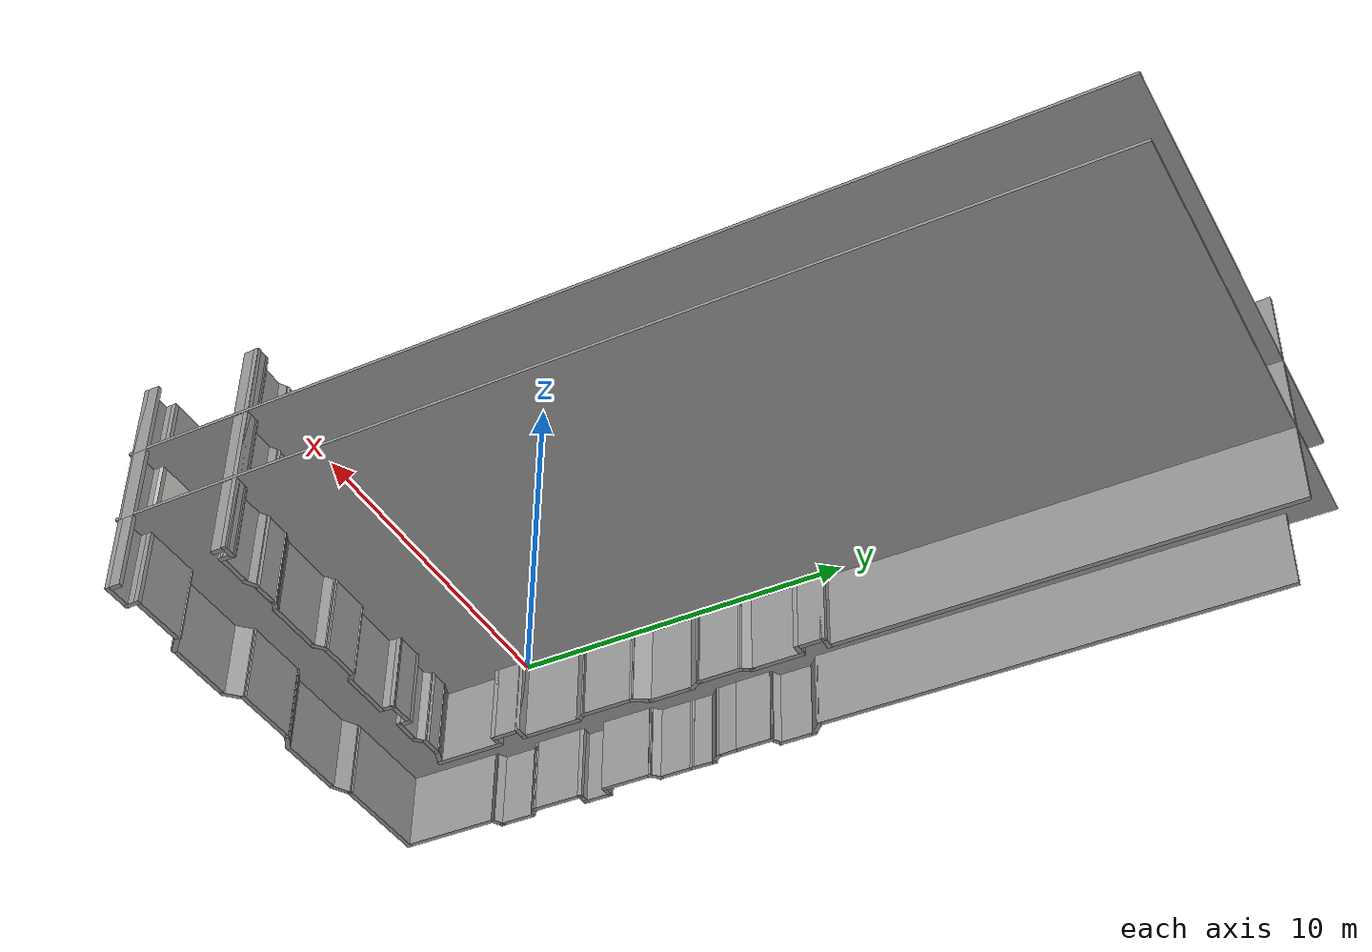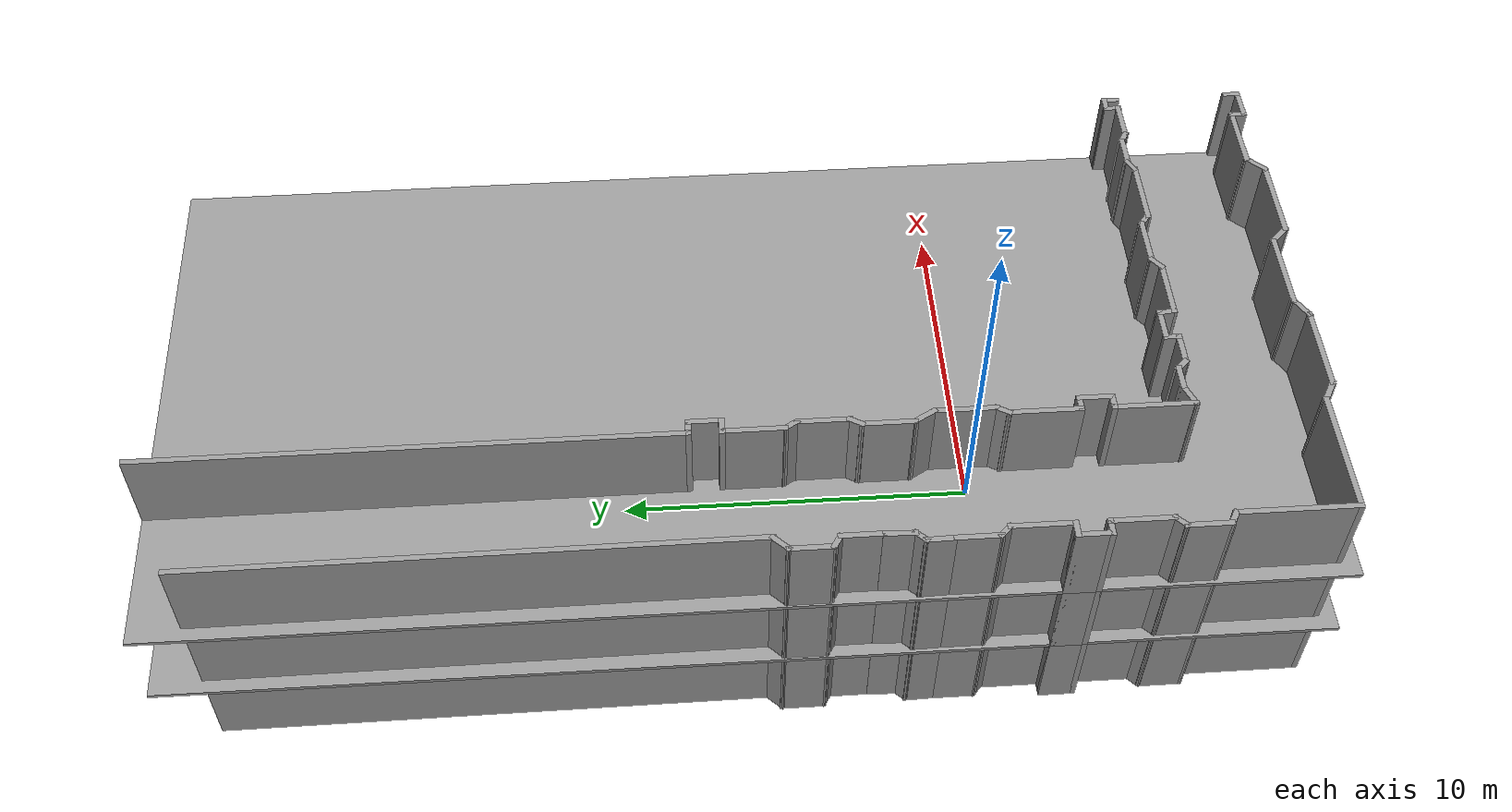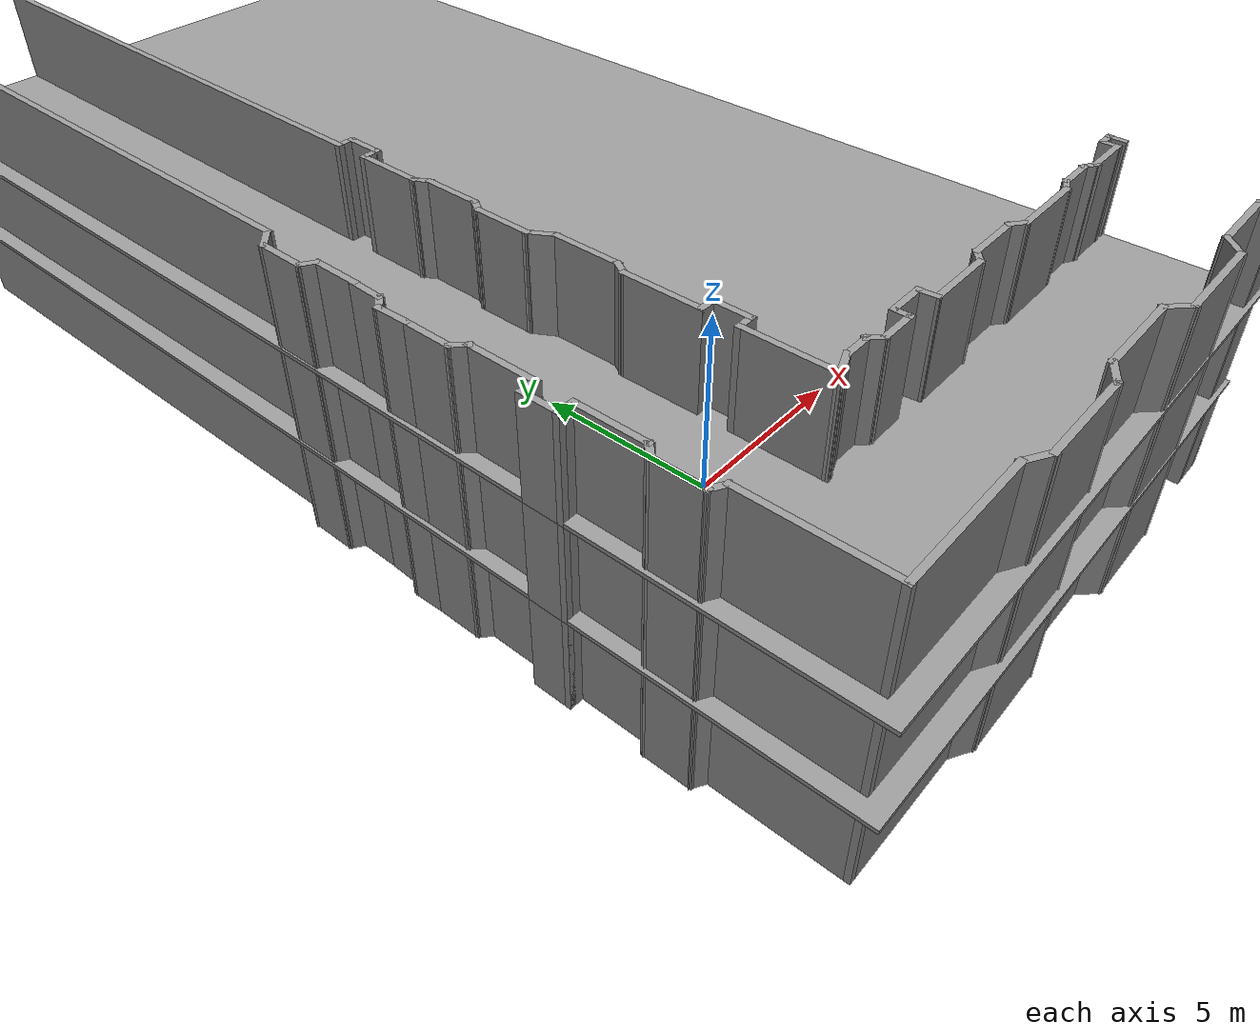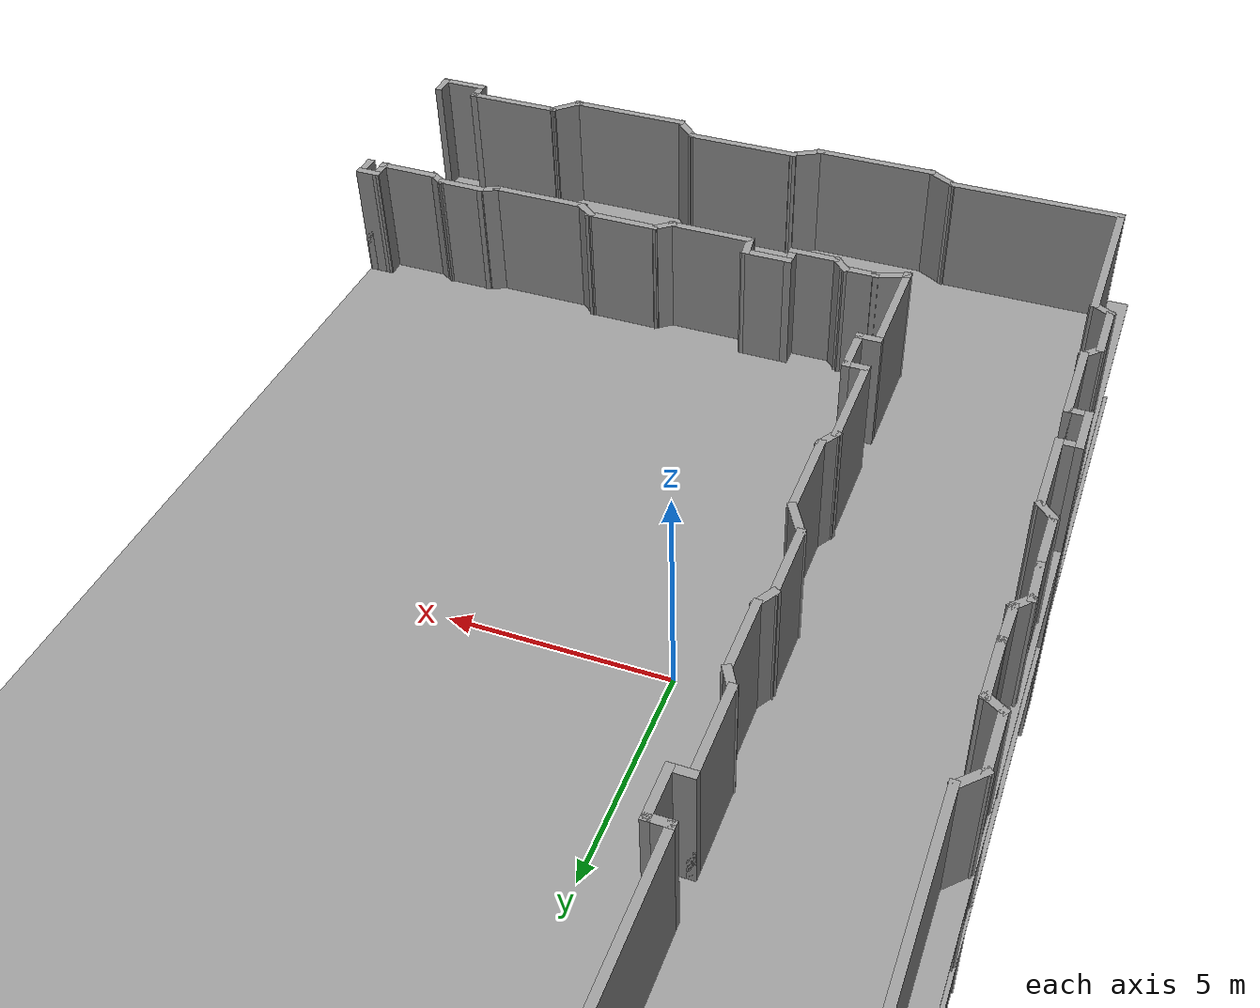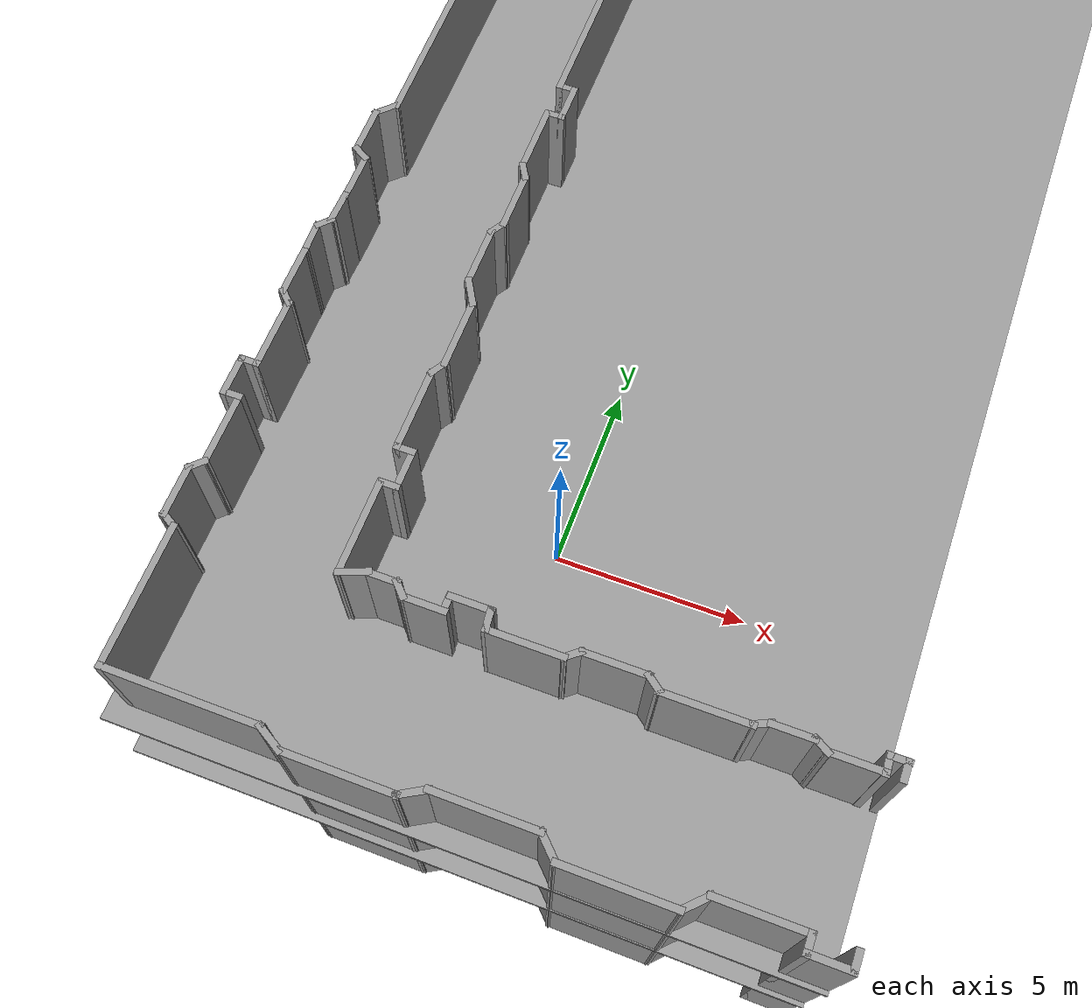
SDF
<?xml version='1.0'?>
<sdf version='1.6'>
  <model name='use_case1_stacked'>
    <pose frame=''>0.822713 6.83476 0 0 -0 0</pose>
    <link name='Floor_7'>
      <collision name='Floor_7_Collision'>
        <geometry>
          <box>
            <size>15.3808 31.0307 0.1</size>
          </box>
        </geometry>
        <pose frame=''>0 0 0.05 0 -0 0</pose>
      </collision>
      <visual name='Floor_7_Visual'>
        <pose frame=''>0 0 0.05 0 -0 0</pose>
        <geometry>
          <box>
            <size>15.3808 31.0307 0.1</size>
          </box>
        </geometry>
        <material>
          <script>
            <uri>file://media/materials/scripts/gazebo.material</uri>
            <name>Gazebo/Grey</name>
          </script>
          <ambient>1 1 1 1</ambient>
        </material>
      </visual>
      <pose frame=''>0 -1e-06 2.5 0 -0 0</pose>
    </link>
    <link name='Floor_8'>
      <collision name='Floor_8_Collision'>
        <geometry>
          <box>
            <size>15.3808 31.0307 0.1</size>
          </box>
        </geometry>
        <pose frame=''>0 0 0.05 0 -0 0</pose>
      </collision>
      <visual name='Floor_8_Visual'>
        <pose frame=''>0 0 0.05 0 -0 0</pose>
        <geometry>
          <box>
            <size>15.3808 31.0307 0.1</size>
          </box>
        </geometry>
        <material>
          <script>
            <uri>file://media/materials/scripts/gazebo.material</uri>
            <name>Gazebo/Grey</name>
          </script>
          <ambient>1 1 1 1</ambient>
        </material>
      </visual>
      <pose frame=''>0 -1e-06 5 0 -0 0</pose>
    </link>
    <link name='Wall_100'>
      <collision name='Wall_100_Collision'>
        <geometry>
          <box>
            <size>0.5 0.15 2.5</size>
          </box>
        </geometry>
        <pose frame=''>0 0 1.25 0 -0 0</pose>
      </collision>
      <visual name='Wall_100_Visual'>
        <pose frame=''>0 0 1.25 0 -0 0</pose>
        <geometry>
          <box>
            <size>0.5 0.15 2.5</size>
          </box>
        </geometry>
        <material>
          <script>
            <uri>file://media/materials/scripts/gazebo.material</uri>
            <name>Gazebo/Grey</name>
          </script>
          <ambient>1 1 1 1</ambient>
        </material>
      </visual>
      <pose frame=''>-3.67133 -6.68702 0 0 0 -2.0944</pose>
    </link>
    <link name='Wall_101'>
      <collision name='Wall_101_Collision'>
        <geometry>
          <box>
            <size>2 0.15 2.5</size>
          </box>
        </geometry>
        <pose frame=''>0 0 1.25 0 -0 0</pose>
      </collision>
      <visual name='Wall_101_Visual'>
        <pose frame=''>0 0 1.25 0 -0 0</pose>
        <geometry>
          <box>
            <size>2 0.15 2.5</size>
          </box>
        </geometry>
        <material>
          <script>
            <uri>file://media/materials/scripts/gazebo.material</uri>
            <name>Gazebo/Grey</name>
          </script>
          <ambient>1 1 1 1</ambient>
        </material>
      </visual>
      <pose frame=''>-3.75883 -7.76357 0 0 0 -1.5708</pose>
    </link>
    <link name='Wall_103'>
      <collision name='Wall_103_Collision'>
        <geometry>
          <box>
            <size>0.5 0.15 2.5</size>
          </box>
        </geometry>
        <pose frame=''>0 0 1.25 0 -0 0</pose>
      </collision>
      <visual name='Wall_103_Visual'>
        <pose frame=''>0 0 1.25 0 -0 0</pose>
        <geometry>
          <box>
            <size>0.5 0.15 2.5</size>
          </box>
        </geometry>
        <material>
          <script>
            <uri>file://media/materials/scripts/gazebo.material</uri>
            <name>Gazebo/Grey</name>
          </script>
          <ambient>1 1 1 1</ambient>
        </material>
      </visual>
      <pose frame=''>-3.58383 -8.68857 0 0 -0 0</pose>
    </link>
    <link name='Wall_104'>
      <collision name='Wall_104_Collision'>
        <geometry>
          <box>
            <size>1 0.15 2.5</size>
          </box>
        </geometry>
        <pose frame=''>0 0 1.25 0 -0 0</pose>
      </collision>
      <visual name='Wall_104_Visual'>
        <pose frame=''>0 0 1.25 0 -0 0</pose>
        <geometry>
          <box>
            <size>1 0.15 2.5</size>
          </box>
        </geometry>
        <material>
          <script>
            <uri>file://media/materials/scripts/gazebo.material</uri>
            <name>Gazebo/Grey</name>
          </script>
          <ambient>1 1 1 1</ambient>
        </material>
      </visual>
      <pose frame=''>-3.40883 -9.11357 0 0 0 -1.5708</pose>
    </link>
    <link name='Wall_105'>
      <collision name='Wall_105_Collision'>
        <geometry>
          <box>
            <size>0.5 0.15 2.5</size>
          </box>
        </geometry>
        <pose frame=''>0 0 1.25 0 -0 0</pose>
      </collision>
      <visual name='Wall_105_Visual'>
        <pose frame=''>0 0 1.25 0 -0 0</pose>
        <geometry>
          <box>
            <size>0.5 0.15 2.5</size>
          </box>
        </geometry>
        <material>
          <script>
            <uri>file://media/materials/scripts/gazebo.material</uri>
            <name>Gazebo/Grey</name>
          </script>
          <ambient>1 1 1 1</ambient>
        </material>
      </visual>
      <pose frame=''>-3.58383 -9.53857 0 0 -0 3.14159</pose>
    </link>
    <link name='Wall_106'>
      <collision name='Wall_106_Collision'>
        <geometry>
          <box>
            <size>2.25 0.15 2.5</size>
          </box>
        </geometry>
        <pose frame=''>0 0 1.25 0 -0 0</pose>
      </collision>
      <visual name='Wall_106_Visual'>
        <pose frame=''>0 0 1.25 0 -0 0</pose>
        <geometry>
          <box>
            <size>2.25 0.15 2.5</size>
          </box>
        </geometry>
        <material>
          <script>
            <uri>file://media/materials/scripts/gazebo.material</uri>
            <name>Gazebo/Grey</name>
          </script>
          <ambient>1 1 1 1</ambient>
        </material>
      </visual>
      <pose frame=''>-3.75883 -10.5886 0 0 0 -1.5708</pose>
    </link>
    <link name='Wall_108'>
      <collision name='Wall_108_Collision'>
        <geometry>
          <box>
            <size>0.740104 0.15 2.5</size>
          </box>
        </geometry>
        <pose frame=''>0 0 1.25 0 -0 0</pose>
      </collision>
      <visual name='Wall_108_Visual'>
        <pose frame=''>0 0 1.25 0 -0 0</pose>
        <geometry>
          <box>
            <size>0.740104 0.15 2.5</size>
          </box>
        </geometry>
        <material>
          <script>
            <uri>file://media/materials/scripts/gazebo.material</uri>
            <name>Gazebo/Grey</name>
          </script>
          <ambient>1 1 1 1</ambient>
        </material>
      </visual>
      <pose frame=''>-3.48434 -11.5303 0 0 -0 0.375606</pose>
    </link>
    <link name='Wall_109'>
      <collision name='Wall_109_Collision'>
        <geometry>
          <box>
            <size>0.75 0.15 2.5</size>
          </box>
        </geometry>
        <pose frame=''>0 0 1.25 0 -0 0</pose>
      </collision>
      <visual name='Wall_109_Visual'>
        <pose frame=''>0 0 1.25 0 -0 0</pose>
        <geometry>
          <box>
            <size>0.75 0.15 2.5</size>
          </box>
        </geometry>
        <material>
          <script>
            <uri>file://media/materials/scripts/gazebo.material</uri>
            <name>Gazebo/Grey</name>
          </script>
          <ambient>1 1 1 1</ambient>
        </material>
      </visual>
      <pose frame=''>-2.89457 -11.4374 0 0 -0 0</pose>
    </link>
    <link name='Wall_110'>
      <collision name='Wall_110_Collision'>
        <geometry>
          <box>
            <size>0.489357 0.15 2.5</size>
          </box>
        </geometry>
        <pose frame=''>0 0 1.25 0 -0 0</pose>
      </collision>
      <visual name='Wall_110_Visual'>
        <pose frame=''>0 0 1.25 0 -0 0</pose>
        <geometry>
          <box>
            <size>0.489357 0.15 2.5</size>
          </box>
        </geometry>
        <material>
          <script>
            <uri>file://media/materials/scripts/gazebo.material</uri>
            <name>Gazebo/Grey</name>
          </script>
          <ambient>1 1 1 1</ambient>
        </material>
      </visual>
      <pose frame=''>-2.49377 -11.5458 0 0 0 -0.817273</pose>
    </link>
    <link name='Wall_111'>
      <collision name='Wall_111_Collision'>
        <geometry>
          <box>
            <size>1 0.15 2.5</size>
          </box>
        </geometry>
        <pose frame=''>0 0 1.25 0 -0 0</pose>
      </collision>
      <visual name='Wall_111_Visual'>
        <pose frame=''>0 0 1.25 0 -0 0</pose>
        <geometry>
          <box>
            <size>1 0.15 2.5</size>
          </box>
        </geometry>
        <material>
          <script>
            <uri>file://media/materials/scripts/gazebo.material</uri>
            <name>Gazebo/Grey</name>
          </script>
          <ambient>1 1 1 1</ambient>
        </material>
      </visual>
      <pose frame=''>-1.93738 -11.6696 0 0 -0 0</pose>
    </link>
    <link name='Wall_112'>
      <collision name='Wall_112_Collision'>
        <geometry>
          <box>
            <size>0.484705 0.15 2.5</size>
          </box>
        </geometry>
        <pose frame=''>0 0 1.25 0 -0 0</pose>
      </collision>
      <visual name='Wall_112_Visual'>
        <pose frame=''>0 0 1.25 0 -0 0</pose>
        <geometry>
          <box>
            <size>0.484705 0.15 2.5</size>
          </box>
        </geometry>
        <material>
          <script>
            <uri>file://media/materials/scripts/gazebo.material</uri>
            <name>Gazebo/Grey</name>
          </script>
          <ambient>1 1 1 1</ambient>
        </material>
      </visual>
      <pose frame=''>-1.52767 -11.5022 0 0 -0 1.5708</pose>
    </link>
    <link name='Wall_113'>
      <collision name='Wall_113_Collision'>
        <geometry>
          <box>
            <size>1 0.15 2.5</size>
          </box>
        </geometry>
        <pose frame=''>0 0 1.25 0 -0 0</pose>
      </collision>
      <visual name='Wall_113_Visual'>
        <pose frame=''>0 0 1.25 0 -0 0</pose>
        <geometry>
          <box>
            <size>1 0.15 2.5</size>
          </box>
        </geometry>
        <material>
          <script>
            <uri>file://media/materials/scripts/gazebo.material</uri>
            <name>Gazebo/Grey</name>
          </script>
          <ambient>1 1 1 1</ambient>
        </material>
      </visual>
      <pose frame=''>-1.08737 -11.3349 0 0 -0 0</pose>
    </link>
    <link name='Wall_114'>
      <collision name='Wall_114_Collision'>
        <geometry>
          <box>
            <size>0.548536 0.15 2.5</size>
          </box>
        </geometry>
        <pose frame=''>0 0 1.25 0 -0 0</pose>
      </collision>
      <visual name='Wall_114_Visual'>
        <pose frame=''>0 0 1.25 0 -0 0</pose>
        <geometry>
          <box>
            <size>0.548536 0.15 2.5</size>
          </box>
        </geometry>
        <material>
          <script>
            <uri>file://media/materials/scripts/gazebo.material</uri>
            <name>Gazebo/Grey</name>
          </script>
          <ambient>1 1 1 1</ambient>
        </material>
      </visual>
      <pose frame=''>-0.654727 -11.5328 0 0 0 -1.45541</pose>
    </link>
    <link name='Wall_115'>
      <collision name='Wall_115_Collision'>
        <geometry>
          <box>
            <size>1.75 0.15 2.5</size>
          </box>
        </geometry>
        <pose frame=''>0 0 1.25 0 -0 0</pose>
      </collision>
      <visual name='Wall_115_Visual'>
        <pose frame=''>0 0 1.25 0 -0 0</pose>
        <geometry>
          <box>
            <size>1.75 0.15 2.5</size>
          </box>
        </geometry>
        <material>
          <script>
            <uri>file://media/materials/scripts/gazebo.material</uri>
            <name>Gazebo/Grey</name>
          </script>
          <ambient>1 1 1 1</ambient>
        </material>
      </visual>
      <pose frame=''>0.168215 -11.7308 0 0 -0 0</pose>
    </link>
    <link name='Wall_116'>
      <collision name='Wall_116_Collision'>
        <geometry>
          <box>
            <size>0.500794 0.15 2.5</size>
          </box>
        </geometry>
        <pose frame=''>0 0 1.25 0 -0 0</pose>
      </collision>
      <visual name='Wall_116_Visual'>
        <pose frame=''>0 0 1.25 0 -0 0</pose>
        <geometry>
          <box>
            <size>0.500794 0.15 2.5</size>
          </box>
        </geometry>
        <material>
          <script>
            <uri>file://media/materials/scripts/gazebo.material</uri>
            <name>Gazebo/Grey</name>
          </script>
          <ambient>1 1 1 1</ambient>
        </material>
      </visual>
      <pose frame=''>1.10448 -11.6203 0 0 -0 0.68113</pose>
    </link>
    <link name='Wall_117'>
      <collision name='Wall_117_Collision'>
        <geometry>
          <box>
            <size>1.5 0.15 2.5</size>
          </box>
        </geometry>
        <pose frame=''>0 0 1.25 0 -0 0</pose>
      </collision>
      <visual name='Wall_117_Visual'>
        <pose frame=''>0 0 1.25 0 -0 0</pose>
        <geometry>
          <box>
            <size>1.5 0.15 2.5</size>
          </box>
        </geometry>
        <material>
          <script>
            <uri>file://media/materials/scripts/gazebo.material</uri>
            <name>Gazebo/Grey</name>
          </script>
          <ambient>1 1 1 1</ambient>
        </material>
      </visual>
      <pose frame=''>1.93103 -11.5099 0 0 -0 0</pose>
    </link>
    <link name='Wall_118'>
      <collision name='Wall_118_Collision'>
        <geometry>
          <box>
            <size>0.502663 0.15 2.5</size>
          </box>
        </geometry>
        <pose frame=''>0 0 1.25 0 -0 0</pose>
      </collision>
      <visual name='Wall_118_Visual'>
        <pose frame=''>0 0 1.25 0 -0 0</pose>
        <geometry>
          <box>
            <size>0.502663 0.15 2.5</size>
          </box>
        </geometry>
        <material>
          <script>
            <uri>file://media/materials/scripts/gazebo.material</uri>
            <name>Gazebo/Grey</name>
          </script>
          <ambient>1 1 1 1</ambient>
        </material>
      </visual>
      <pose frame=''>2.72977 -11.6183 0 0 0 -0.662419</pose>
    </link>
    <link name='Wall_119'>
      <collision name='Wall_119_Collision'>
        <geometry>
          <box>
            <size>2 0.15 2.5</size>
          </box>
        </geometry>
        <pose frame=''>0 0 1.25 0 -0 0</pose>
      </collision>
      <visual name='Wall_119_Visual'>
        <pose frame=''>0 0 1.25 0 -0 0</pose>
        <geometry>
          <box>
            <size>2 0.15 2.5</size>
          </box>
        </geometry>
        <material>
          <script>
            <uri>file://media/materials/scripts/gazebo.material</uri>
            <name>Gazebo/Grey</name>
          </script>
          <ambient>1 1 1 1</ambient>
        </material>
      </visual>
      <pose frame=''>3.79381 -11.7421 0 0 -0 0</pose>
    </link>
    <link name='Wall_120'>
      <collision name='Wall_120_Collision'>
        <geometry>
          <box>
            <size>0.485752 0.15 2.5</size>
          </box>
        </geometry>
        <pose frame=''>0 0 1.25 0 -0 0</pose>
      </collision>
      <visual name='Wall_120_Visual'>
        <pose frame=''>0 0 1.25 0 -0 0</pose>
        <geometry>
          <box>
            <size>0.485752 0.15 2.5</size>
          </box>
        </geometry>
        <material>
          <script>
            <uri>file://media/materials/scripts/gazebo.material</uri>
            <name>Gazebo/Grey</name>
          </script>
          <ambient>1 1 1 1</ambient>
        </material>
      </visual>
      <pose frame=''>4.87037 -11.6546 0 0 -0 0.444613</pose>
    </link>
    <link name='Wall_121'>
      <collision name='Wall_121_Collision'>
        <geometry>
          <box>
            <size>1 0.15 2.5</size>
          </box>
        </geometry>
        <pose frame=''>0 0 1.25 0 -0 0</pose>
      </collision>
      <visual name='Wall_121_Visual'>
        <pose frame=''>0 0 1.25 0 -0 0</pose>
        <geometry>
          <box>
            <size>1 0.15 2.5</size>
          </box>
        </geometry>
        <material>
          <script>
            <uri>file://media/materials/scripts/gazebo.material</uri>
            <name>Gazebo/Grey</name>
          </script>
          <ambient>1 1 1 1</ambient>
        </material>
      </visual>
      <pose frame=''>5.44692 -11.5977 0 0 -0 0</pose>
    </link>
    <link name='Wall_122'>
      <collision name='Wall_122_Collision'>
        <geometry>
          <box>
            <size>0.486841 0.15 2.5</size>
          </box>
        </geometry>
        <pose frame=''>0 0 1.25 0 -0 0</pose>
      </collision>
      <visual name='Wall_122_Visual'>
        <pose frame=''>0 0 1.25 0 -0 0</pose>
        <geometry>
          <box>
            <size>0.486841 0.15 2.5</size>
          </box>
        </geometry>
        <material>
          <script>
            <uri>file://media/materials/scripts/gazebo.material</uri>
            <name>Gazebo/Grey</name>
          </script>
          <ambient>1 1 1 1</ambient>
        </material>
      </visual>
      <pose frame=''>6.01583 -11.6699 0 0 0 -0.546304</pose>
    </link>
    <link name='Wall_123'>
      <collision name='Wall_123_Collision'>
        <geometry>
          <box>
            <size>1.25 0.15 2.5</size>
          </box>
        </geometry>
        <pose frame=''>0 0 1.25 0 -0 0</pose>
      </collision>
      <visual name='Wall_123_Visual'>
        <pose frame=''>0 0 1.25 0 -0 0</pose>
        <geometry>
          <box>
            <size>1.25 0.15 2.5</size>
          </box>
        </geometry>
        <material>
          <script>
            <uri>file://media/materials/scripts/gazebo.material</uri>
            <name>Gazebo/Grey</name>
          </script>
          <ambient>1 1 1 1</ambient>
        </material>
      </visual>
      <pose frame=''>6.70973 -11.7421 0 0 -0 0</pose>
    </link>
    <link name='Wall_124'>
      <collision name='Wall_124_Collision'>
        <geometry>
          <box>
            <size>0.500334 0.15 2.5</size>
          </box>
        </geometry>
        <pose frame=''>0 0 1.25 0 -0 0</pose>
      </collision>
      <visual name='Wall_124_Visual'>
        <pose frame=''>0 0 1.25 0 -0 0</pose>
        <geometry>
          <box>
            <size>0.500334 0.15 2.5</size>
          </box>
        </geometry>
        <material>
          <script>
            <uri>file://media/materials/scripts/gazebo.material</uri>
            <name>Gazebo/Grey</name>
          </script>
          <ambient>1 1 1 1</ambient>
        </material>
      </visual>
      <pose frame=''>7.25209 -11.5824 0 0 -0 1.61447</pose>
    </link>
    <link name='Wall_125'>
      <collision name='Wall_125_Collision'>
        <geometry>
          <box>
            <size>0.5 0.15 2.5</size>
          </box>
        </geometry>
        <pose frame=''>0 0 1.25 0 -0 0</pose>
      </collision>
      <visual name='Wall_125_Visual'>
        <pose frame=''>0 0 1.25 0 -0 0</pose>
        <geometry>
          <box>
            <size>0.5 0.15 2.5</size>
          </box>
        </geometry>
        <material>
          <script>
            <uri>file://media/materials/scripts/gazebo.material</uri>
            <name>Gazebo/Grey</name>
          </script>
          <ambient>1 1 1 1</ambient>
        </material>
      </visual>
      <pose frame=''>7.43473 -11.4074 0 0 -0 0</pose>
    </link>
    <link name='Wall_126'>
      <collision name='Wall_126_Collision'>
        <geometry>
          <box>
            <size>0.5 0.15 2.5</size>
          </box>
        </geometry>
        <pose frame=''>0 0 1.25 0 -0 0</pose>
      </collision>
      <visual name='Wall_126_Visual'>
        <pose frame=''>0 0 1.25 0 -0 0</pose>
        <geometry>
          <box>
            <size>0.5 0.15 2.5</size>
          </box>
        </geometry>
        <material>
          <script>
            <uri>file://media/materials/scripts/gazebo.material</uri>
            <name>Gazebo/Grey</name>
          </script>
          <ambient>1 1 1 1</ambient>
        </material>
      </visual>
      <pose frame=''>7.59444 -11.5824 0 0 0 -1.5708</pose>
    </link>
    <link name='Wall_262'>
      <collision name='Wall_262_Collision'>
        <geometry>
          <box>
            <size>0.5 0.15 2.5</size>
          </box>
        </geometry>
        <pose frame=''>0 0 1.25 0 -0 0</pose>
      </collision>
      <visual name='Wall_262_Visual'>
        <pose frame=''>0 0 1.25 0 -0 0</pose>
        <geometry>
          <box>
            <size>0.5 0.15 2.5</size>
          </box>
        </geometry>
        <material>
          <script>
            <uri>file://media/materials/scripts/gazebo.material</uri>
            <name>Gazebo/Grey</name>
          </script>
          <ambient>1 1 1 1</ambient>
        </material>
      </visual>
      <pose frame=''>7.61542 -15.16 2.5 0 0 -1.5708</pose>
    </link>
    <link name='Wall_263'>
      <collision name='Wall_263_Collision'>
        <geometry>
          <box>
            <size>1 0.15 2.5</size>
          </box>
        </geometry>
        <pose frame=''>0 0 1.25 0 -0 0</pose>
      </collision>
      <visual name='Wall_263_Visual'>
        <pose frame=''>0 0 1.25 0 -0 0</pose>
        <geometry>
          <box>
            <size>1 0.15 2.5</size>
          </box>
        </geometry>
        <material>
          <script>
            <uri>file://media/materials/scripts/gazebo.material</uri>
            <name>Gazebo/Grey</name>
          </script>
          <ambient>1 1 1 1</ambient>
        </material>
      </visual>
      <pose frame=''>7.19042 -15.335 2.5 0 -0 3.14159</pose>
    </link>
    <link name='Wall_264'>
      <collision name='Wall_264_Collision'>
        <geometry>
          <box>
            <size>0.5 0.15 2.5</size>
          </box>
        </geometry>
        <pose frame=''>0 0 1.25 0 -0 0</pose>
      </collision>
      <visual name='Wall_264_Visual'>
        <pose frame=''>0 0 1.25 0 -0 0</pose>
        <geometry>
          <box>
            <size>0.5 0.15 2.5</size>
          </box>
        </geometry>
        <material>
          <script>
            <uri>file://media/materials/scripts/gazebo.material</uri>
            <name>Gazebo/Grey</name>
          </script>
          <ambient>1 1 1 1</ambient>
        </material>
      </visual>
      <pose frame=''>6.76541 -15.16 2.5 0 -0 1.5708</pose>
    </link>
    <link name='Wall_265'>
      <collision name='Wall_265_Collision'>
        <geometry>
          <box>
            <size>2 0.15 2.5</size>
          </box>
        </geometry>
        <pose frame=''>0 0 1.25 0 -0 0</pose>
      </collision>
      <visual name='Wall_265_Visual'>
        <pose frame=''>0 0 1.25 0 -0 0</pose>
        <geometry>
          <box>
            <size>2 0.15 2.5</size>
          </box>
        </geometry>
        <material>
          <script>
            <uri>file://media/materials/scripts/gazebo.material</uri>
            <name>Gazebo/CeilingTiled</name>
          </script>
          <ambient>1 1 1 1</ambient>
        </material>
      </visual>
      <pose frame=''>5.84042 -14.985 2.5 0 -0 3.14159</pose>
    </link>
    <link name='Wall_266'>
      <collision name='Wall_266_Collision'>
        <geometry>
          <box>
            <size>0.75 0.15 2.5</size>
          </box>
        </geometry>
        <pose frame=''>0 0 1.25 0 -0 0</pose>
      </collision>
      <visual name='Wall_266_Visual'>
        <pose frame=''>0 0 1.25 0 -0 0</pose>
        <geometry>
          <box>
            <size>0.75 0.15 2.5</size>
          </box>
        </geometry>
        <material>
          <script>
            <uri>file://media/materials/scripts/gazebo.material</uri>
            <name>Gazebo/Grey</name>
          </script>
          <ambient>1 1 1 1</ambient>
        </material>
      </visual>
      <pose frame=''>4.70328 -15.1972 2.5 0 0 -2.35619</pose>
    </link>
    <link name='Wall_267'>
      <collision name='Wall_267_Collision'>
        <geometry>
          <box>
            <size>2.5 0.15 2.5</size>
          </box>
        </geometry>
        <pose frame=''>0 0 1.25 0 -0 0</pose>
      </collision>
      <visual name='Wall_267_Visual'>
        <pose frame=''>0 0 1.25 0 -0 0</pose>
        <geometry>
          <box>
            <size>2.5 0.15 2.5</size>
          </box>
        </geometry>
        <material>
          <script>
            <uri>file://media/materials/scripts/gazebo.material</uri>
            <name>Gazebo/Grey</name>
          </script>
          <ambient>1 1 1 1</ambient>
        </material>
      </visual>
      <pose frame=''>3.31615 -15.4093 2.5 0 -0 3.14159</pose>
    </link>
    <link name='Wall_268'>
      <collision name='Wall_268_Collision'>
        <geometry>
          <box>
            <size>0.75 0.15 2.5</size>
          </box>
        </geometry>
        <pose frame=''>0 0 1.25 0 -0 0</pose>
      </collision>
      <visual name='Wall_268_Visual'>
        <pose frame=''>0 0 1.25 0 -0 0</pose>
        <geometry>
          <box>
            <size>0.75 0.15 2.5</size>
          </box>
        </geometry>
        <material>
          <script>
            <uri>file://media/materials/scripts/gazebo.material</uri>
            <name>Gazebo/Grey</name>
          </script>
          <ambient>1 1 1 1</ambient>
        </material>
      </visual>
      <pose frame=''>1.92902 -15.1972 2.5 0 -0 2.35619</pose>
    </link>
    <link name='Wall_269'>
      <collision name='Wall_269_Collision'>
        <geometry>
          <box>
            <size>2.35494 0.15 2.5</size>
          </box>
        </geometry>
        <pose frame=''>0 0 1.25 0 -0 0</pose>
      </collision>
      <visual name='Wall_269_Visual'>
        <pose frame=''>0 0 1.25 0 -0 0</pose>
        <geometry>
          <box>
            <size>2.35494 0.15 2.5</size>
          </box>
        </geometry>
        <material>
          <script>
            <uri>file://media/materials/scripts/gazebo.material</uri>
            <name>Gazebo/Grey</name>
          </script>
          <ambient>1 1 1 1</ambient>
        </material>
      </visual>
      <pose frame=''>0.614417 -14.985 2.5 0 -0 3.14159</pose>
    </link>
    <link name='Wall_270'>
      <collision name='Wall_270_Collision'>
        <geometry>
          <box>
            <size>0.75 0.15 2.5</size>
          </box>
        </geometry>
        <pose frame=''>0 0 1.25 0 -0 0</pose>
      </collision>
      <visual name='Wall_270_Visual'>
        <pose frame=''>0 0 1.25 0 -0 0</pose>
        <geometry>
          <box>
            <size>0.75 0.15 2.5</size>
          </box>
        </geometry>
        <material>
          <script>
            <uri>file://media/materials/scripts/gazebo.material</uri>
            <name>Gazebo/Grey</name>
          </script>
          <ambient>1 1 1 1</ambient>
        </material>
      </visual>
      <pose frame=''>-0.730371 -15.135 2.5 0 0 -2.61799</pose>
    </link>
    <link name='Wall_271'>
      <collision name='Wall_271_Collision'>
        <geometry>
          <box>
            <size>2.5 0.15 2.5</size>
          </box>
        </geometry>
        <pose frame=''>0 0 1.25 0 -0 0</pose>
      </collision>
      <visual name='Wall_271_Visual'>
        <pose frame=''>0 0 1.25 0 -0 0</pose>
        <geometry>
          <box>
            <size>2.5 0.15 2.5</size>
          </box>
        </geometry>
        <material>
          <script>
            <uri>file://media/materials/scripts/gazebo.material</uri>
            <name>Gazebo/Grey</name>
          </script>
          <ambient>1 1 1 1</ambient>
        </material>
      </visual>
      <pose frame=''>-2.16518 -15.285 2.5 0 -0 3.14159</pose>
    </link>
    <link name='Wall_272'>
      <collision name='Wall_272_Collision'>
        <geometry>
          <box>
            <size>0.75 0.15 2.5</size>
          </box>
        </geometry>
        <pose frame=''>0 0 1.25 0 -0 0</pose>
      </collision>
      <visual name='Wall_272_Visual'>
        <pose frame=''>0 0 1.25 0 -0 0</pose>
        <geometry>
          <box>
            <size>0.75 0.15 2.5</size>
          </box>
        </geometry>
        <material>
          <script>
            <uri>file://media/materials/scripts/gazebo.material</uri>
            <name>Gazebo/Grey</name>
          </script>
          <ambient>1 1 1 1</ambient>
        </material>
      </visual>
      <pose frame=''>-3.59999 -15.135 2.5 0 -0 2.61799</pose>
    </link>
    <link name='Wall_273'>
      <collision name='Wall_273_Collision'>
        <geometry>
          <box>
            <size>3.5 0.15 2.5</size>
          </box>
        </geometry>
        <pose frame=''>0 0 1.25 0 -0 0</pose>
      </collision>
      <visual name='Wall_273_Visual'>
        <pose frame=''>0 0 1.25 0 -0 0</pose>
        <geometry>
          <box>
            <size>3.5 0.15 2.5</size>
          </box>
        </geometry>
        <material>
          <script>
            <uri>file://media/materials/scripts/gazebo.material</uri>
            <name>Gazebo/Grey</name>
          </script>
          <ambient>1 1 1 1</ambient>
        </material>
      </visual>
      <pose frame=''>-5.53479 -14.985 2.5 0 -0 3.14159</pose>
    </link>
    <link name='Wall_274'>
      <collision name='Wall_274_Collision'>
        <geometry>
          <box>
            <size>3.25 0.15 2.5</size>
          </box>
        </geometry>
        <pose frame=''>0 0 1.25 0 -0 0</pose>
      </collision>
      <visual name='Wall_274_Visual'>
        <pose frame=''>0 0 1.25 0 -0 0</pose>
        <geometry>
          <box>
            <size>3.25 0.15 2.5</size>
          </box>
        </geometry>
        <material>
          <script>
            <uri>file://media/materials/scripts/gazebo.material</uri>
            <name>Gazebo/Grey</name>
          </script>
          <ambient>1 1 1 1</ambient>
        </material>
      </visual>
      <pose frame=''>-7.20979 -13.435 2.5 0 -0 1.5708</pose>
    </link>
    <link name='Wall_275'>
      <collision name='Wall_275_Collision'>
        <geometry>
          <box>
            <size>0.5 0.15 2.5</size>
          </box>
        </geometry>
        <pose frame=''>0 0 1.25 0 -0 0</pose>
      </collision>
      <visual name='Wall_275_Visual'>
        <pose frame=''>0 0 1.25 0 -0 0</pose>
        <geometry>
          <box>
            <size>0.5 0.15 2.5</size>
          </box>
        </geometry>
        <material>
          <script>
            <uri>file://media/materials/scripts/gazebo.material</uri>
            <name>Gazebo/Grey</name>
          </script>
          <ambient>1 1 1 1</ambient>
        </material>
      </visual>
      <pose frame=''>-7.36135 -11.7975 2.5 0 -0 2.61799</pose>
    </link>
    <link name='Wall_276'>
      <collision name='Wall_276_Collision'>
        <geometry>
          <box>
            <size>1.25 0.15 2.5</size>
          </box>
        </geometry>
        <pose frame=''>0 0 1.25 0 -0 0</pose>
      </collision>
      <visual name='Wall_276_Visual'>
        <pose frame=''>0 0 1.25 0 -0 0</pose>
        <geometry>
          <box>
            <size>1.25 0.15 2.5</size>
          </box>
        </geometry>
        <material>
          <script>
            <uri>file://media/materials/scripts/gazebo.material</uri>
            <name>Gazebo/Grey</name>
          </script>
          <ambient>1 1 1 1</ambient>
        </material>
      </visual>
      <pose frame=''>-7.5129 -11.16 2.5 0 -0 1.5708</pose>
    </link>
    <link name='Wall_277'>
      <collision name='Wall_277_Collision'>
        <geometry>
          <box>
            <size>0.5 0.15 2.5</size>
          </box>
        </geometry>
        <pose frame=''>0 0 1.25 0 -0 0</pose>
      </collision>
      <visual name='Wall_277_Visual'>
        <pose frame=''>0 0 1.25 0 -0 0</pose>
        <geometry>
          <box>
            <size>0.5 0.15 2.5</size>
          </box>
        </geometry>
        <material>
          <script>
            <uri>file://media/materials/scripts/gazebo.material</uri>
            <name>Gazebo/Grey</name>
          </script>
          <ambient>1 1 1 1</ambient>
        </material>
      </visual>
      <pose frame=''>-7.38916 -10.4863 2.5 0 -0 0.785398</pose>
    </link>
    <link name='Wall_278'>
      <collision name='Wall_278_Collision'>
        <geometry>
          <box>
            <size>1.75 0.15 2.5</size>
          </box>
        </geometry>
        <pose frame=''>0 0 1.25 0 -0 0</pose>
      </collision>
      <visual name='Wall_278_Visual'>
        <pose frame=''>0 0 1.25 0 -0 0</pose>
        <geometry>
          <box>
            <size>1.75 0.15 2.5</size>
          </box>
        </geometry>
        <material>
          <script>
            <uri>file://media/materials/scripts/gazebo.material</uri>
            <name>Gazebo/Grey</name>
          </script>
          <ambient>1 1 1 1</ambient>
        </material>
      </visual>
      <pose frame=''>-7.26541 -9.56256 2.5 0 -0 1.5708</pose>
    </link>
    <link name='Wall_279'>
      <collision name='Wall_279_Collision'>
        <geometry>
          <box>
            <size>0.5 0.15 2.5</size>
          </box>
        </geometry>
        <pose frame=''>0 0 1.25 0 -0 0</pose>
      </collision>
      <visual name='Wall_279_Visual'>
        <pose frame=''>0 0 1.25 0 -0 0</pose>
        <geometry>
          <box>
            <size>0.5 0.15 2.5</size>
          </box>
        </geometry>
        <material>
          <script>
            <uri>file://media/materials/scripts/gazebo.material</uri>
            <name>Gazebo/Grey</name>
          </script>
          <ambient>1 1 1 1</ambient>
        </material>
      </visual>
      <pose frame=''>-7.44041 -8.76256 2.5 0 -0 3.14159</pose>
    </link>
    <link name='Wall_280'>
      <collision name='Wall_280_Collision'>
        <geometry>
          <box>
            <size>1 0.15 2.5</size>
          </box>
        </geometry>
        <pose frame=''>0 0 1.25 0 -0 0</pose>
      </collision>
      <visual name='Wall_280_Visual'>
        <pose frame=''>0 0 1.25 0 -0 0</pose>
        <geometry>
          <box>
            <size>1 0.15 2.5</size>
          </box>
        </geometry>
        <material>
          <script>
            <uri>file://media/materials/scripts/gazebo.material</uri>
            <name>Gazebo/Grey</name>
          </script>
          <ambient>1 1 1 1</ambient>
        </material>
      </visual>
      <pose frame=''>-7.61541 -8.33756 2.5 0 -0 1.5708</pose>
    </link>
    <link name='Wall_281'>
      <collision name='Wall_281_Collision'>
        <geometry>
          <box>
            <size>0.5 0.15 2.5</size>
          </box>
        </geometry>
        <pose frame=''>0 0 1.25 0 -0 0</pose>
      </collision>
      <visual name='Wall_281_Visual'>
        <pose frame=''>0 0 1.25 0 -0 0</pose>
        <geometry>
          <box>
            <size>0.5 0.15 2.5</size>
          </box>
        </geometry>
        <material>
          <script>
            <uri>file://media/materials/scripts/gazebo.material</uri>
            <name>Gazebo/Grey</name>
          </script>
          <ambient>1 1 1 1</ambient>
        </material>
      </visual>
      <pose frame=''>-7.44041 -7.91256 2.5 0 -0 0</pose>
    </link>
    <link name='Wall_282'>
      <collision name='Wall_282_Collision'>
        <geometry>
          <box>
            <size>1.75 0.15 2.5</size>
          </box>
        </geometry>
        <pose frame=''>0 0 1.25 0 -0 0</pose>
      </collision>
      <visual name='Wall_282_Visual'>
        <pose frame=''>0 0 1.25 0 -0 0</pose>
        <geometry>
          <box>
            <size>1.75 0.15 2.5</size>
          </box>
        </geometry>
        <material>
          <script>
            <uri>file://media/materials/scripts/gazebo.material</uri>
            <name>Gazebo/Grey</name>
          </script>
          <ambient>1 1 1 1</ambient>
        </material>
      </visual>
      <pose frame=''>-7.26541 -7.11256 2.5 0 -0 1.5708</pose>
    </link>
    <link name='Wall_283'>
      <collision name='Wall_283_Collision'>
        <geometry>
          <box>
            <size>0.5 0.15 2.5</size>
          </box>
        </geometry>
        <pose frame=''>0 0 1.25 0 -0 0</pose>
      </collision>
      <visual name='Wall_283_Visual'>
        <pose frame=''>0 0 1.25 0 -0 0</pose>
        <geometry>
          <box>
            <size>0.5 0.15 2.5</size>
          </box>
        </geometry>
        <material>
          <script>
            <uri>file://media/materials/scripts/gazebo.material</uri>
            <name>Gazebo/Grey</name>
          </script>
          <ambient>1 1 1 1</ambient>
        </material>
      </visual>
      <pose frame=''>-7.38916 -6.18881 2.5 0 -0 2.35619</pose>
    </link>
    <link name='Wall_284'>
      <collision name='Wall_284_Collision'>
        <geometry>
          <box>
            <size>1.25 0.15 2.5</size>
          </box>
        </geometry>
        <pose frame=''>0 0 1.25 0 -0 0</pose>
      </collision>
      <visual name='Wall_284_Visual'>
        <pose frame=''>0 0 1.25 0 -0 0</pose>
        <geometry>
          <box>
            <size>1.25 0.15 2.5</size>
          </box>
        </geometry>
        <material>
          <script>
            <uri>file://media/materials/scripts/gazebo.material</uri>
            <name>Gazebo/Grey</name>
          </script>
          <ambient>1 1 1 1</ambient>
        </material>
      </visual>
      <pose frame=''>-7.5129 -5.51507 2.5 0 -0 1.5708</pose>
    </link>
    <link name='Wall_285'>
      <collision name='Wall_285_Collision'>
        <geometry>
          <box>
            <size>0.881015 0.15 2.5</size>
          </box>
        </geometry>
        <pose frame=''>0 0 1.25 0 -0 0</pose>
      </collision>
      <visual name='Wall_285_Visual'>
        <pose frame=''>0 0 1.25 0 -0 0</pose>
        <geometry>
          <box>
            <size>0.881015 0.15 2.5</size>
          </box>
        </geometry>
        <material>
          <script>
            <uri>file://media/materials/scripts/gazebo.material</uri>
            <name>Gazebo/Grey</name>
          </script>
          <ambient>1 1 1 1</ambient>
        </material>
      </visual>
      <pose frame=''>-7.52296 -4.5997 2.5 0 -0 1.59831</pose>
    </link>
    <link name='Wall_286'>
      <collision name='Wall_286_Collision'>
        <geometry>
          <box>
            <size>0.486079 0.15 2.5</size>
          </box>
        </geometry>
        <pose frame=''>0 0 1.25 0 -0 0</pose>
      </collision>
      <visual name='Wall_286_Visual'>
        <pose frame=''>0 0 1.25 0 -0 0</pose>
        <geometry>
          <box>
            <size>0.486079 0.15 2.5</size>
          </box>
        </geometry>
        <material>
          <script>
            <uri>file://media/materials/scripts/gazebo.material</uri>
            <name>Gazebo/Grey</name>
          </script>
          <ambient>1 1 1 1</ambient>
        </material>
      </visual>
      <pose frame=''>-7.40927 -4.11059 2.5 0 -0 0.82773</pose>
    </link>
    <link name='Wall_287'>
      <collision name='Wall_287_Collision'>
        <geometry>
          <box>
            <size>0.869543 0.15 2.5</size>
          </box>
        </geometry>
        <pose frame=''>0 0 1.25 0 -0 0</pose>
      </collision>
      <visual name='Wall_287_Visual'>
        <pose frame=''>0 0 1.25 0 -0 0</pose>
        <geometry>
          <box>
            <size>0.869543 0.15 2.5</size>
          </box>
        </geometry>
        <material>
          <script>
            <uri>file://media/materials/scripts/gazebo.material</uri>
            <name>Gazebo/Grey</name>
          </script>
          <ambient>1 1 1 1</ambient>
        </material>
      </visual>
      <pose frame=''>-7.29558 -3.62721 2.5 0 -0 1.54284</pose>
    </link>
    <link name='Wall_288'>
      <collision name='Wall_288_Collision'>
        <geometry>
          <box>
            <size>1.25 0.15 2.5</size>
          </box>
        </geometry>
        <pose frame=''>0 0 1.25 0 -0 0</pose>
      </collision>
      <visual name='Wall_288_Visual'>
        <pose frame=''>0 0 1.25 0 -0 0</pose>
        <geometry>
          <box>
            <size>1.25 0.15 2.5</size>
          </box>
        </geometry>
        <material>
          <script>
            <uri>file://media/materials/scripts/gazebo.material</uri>
            <name>Gazebo/Grey</name>
          </script>
          <ambient>1 1 1 1</ambient>
        </material>
      </visual>
      <pose frame=''>-7.27547 -2.71758 2.5 0 -0 1.5708</pose>
    </link>
    <link name='Wall_289'>
      <collision name='Wall_289_Collision'>
        <geometry>
          <box>
            <size>0.482733 0.15 2.5</size>
          </box>
        </geometry>
        <pose frame=''>0 0 1.25 0 -0 0</pose>
      </collision>
      <visual name='Wall_289_Visual'>
        <pose frame=''>0 0 1.25 0 -0 0</pose>
        <geometry>
          <box>
            <size>0.482733 0.15 2.5</size>
          </box>
        </geometry>
        <material>
          <script>
            <uri>file://media/materials/scripts/gazebo.material</uri>
            <name>Gazebo/Grey</name>
          </script>
          <ambient>1 1 1 1</ambient>
        </material>
      </visual>
      <pose frame=''>-7.42703 -2.08008 2.5 0 -0 2.58777</pose>
    </link>
    <link name='Wall_290'>
      <collision name='Wall_290_Collision'>
        <geometry>
          <box>
            <size>1.25 0.15 2.5</size>
          </box>
        </geometry>
        <pose frame=''>0 0 1.25 0 -0 0</pose>
      </collision>
      <visual name='Wall_290_Visual'>
        <pose frame=''>0 0 1.25 0 -0 0</pose>
        <geometry>
          <box>
            <size>1.25 0.15 2.5</size>
          </box>
        </geometry>
        <material>
          <script>
            <uri>file://media/materials/scripts/gazebo.material</uri>
            <name>Gazebo/Grey</name>
          </script>
          <ambient>1 1 1 1</ambient>
        </material>
      </visual>
      <pose frame=''>-7.56852 -1.44258 2.5 0 -0 1.5708</pose>
    </link>
    <link name='Wall_291'>
      <collision name='Wall_291_Collision'>
        <geometry>
          <box>
            <size>0.645012 0.15 2.5</size>
          </box>
        </geometry>
        <pose frame=''>0 0 1.25 0 -0 0</pose>
      </collision>
      <visual name='Wall_291_Visual'>
        <pose frame=''>0 0 1.25 0 -0 0</pose>
        <geometry>
          <box>
            <size>0.645012 0.15 2.5</size>
          </box>
        </geometry>
        <material>
          <script>
            <uri>file://media/materials/scripts/gazebo.material</uri>
            <name>Gazebo/Grey</name>
          </script>
          <ambient>1 1 1 1</ambient>
        </material>
      </visual>
      <pose frame=''>-7.39572 -0.715387 2.5 0 -0 0.797941</pose>
    </link>
    <link name='Wall_292'>
      <collision name='Wall_292_Collision'>
        <geometry>
          <box>
            <size>14.7632 0.15 2.5</size>
          </box>
        </geometry>
        <pose frame=''>0 0 1.25 0 -0 0</pose>
      </collision>
      <visual name='Wall_292_Visual'>
        <pose frame=''>0 0 1.25 0 -0 0</pose>
        <geometry>
          <box>
            <size>14.7632 0.15 2.5</size>
          </box>
        </geometry>
        <material>
          <script>
            <uri>file://media/materials/scripts/gazebo.material</uri>
            <name>Gazebo/Grey</name>
          </script>
          <ambient>1 1 1 1</ambient>
        </material>
      </visual>
      <pose frame=''>-7.23034 6.76836 2.5 0 -0 1.575</pose>
    </link>
    <link name='Wall_293'>
      <collision name='Wall_293_Collision'>
        <geometry>
          <box>
            <size>0.5 0.15 2.5</size>
          </box>
        </geometry>
        <pose frame=''>0 0 1.25 0 -0 0</pose>
      </collision>
      <visual name='Wall_293_Visual'>
        <pose frame=''>0 0 1.25 0 -0 0</pose>
        <geometry>
          <box>
            <size>0.5 0.15 2.5</size>
          </box>
        </geometry>
        <material>
          <script>
            <uri>file://media/materials/scripts/gazebo.material</uri>
            <name>Gazebo/Grey</name>
          </script>
          <ambient>1 1 1 1</ambient>
        </material>
      </visual>
      <pose frame=''>-3.70883 1.34037 2.5 0 -0 0</pose>
    </link>
    <link name='Wall_294'>
      <collision name='Wall_294_Collision'>
        <geometry>
          <box>
            <size>14.25 0.15 2.5</size>
          </box>
        </geometry>
        <pose frame=''>0 0 1.25 0 -0 0</pose>
      </collision>
      <visual name='Wall_294_Visual'>
        <pose frame=''>0 0 1.25 0 -0 0</pose>
        <geometry>
          <box>
            <size>14.25 0.15 2.5</size>
          </box>
        </geometry>
        <material>
          <script>
            <uri>file://media/materials/scripts/gazebo.material</uri>
            <name>Gazebo/Grey</name>
          </script>
          <ambient>1 1 1 1</ambient>
        </material>
      </visual>
      <pose frame=''>-3.88383 8.39037 2.5 0 -0 1.5708</pose>
    </link>
    <link name='Wall_295'>
      <collision name='Wall_295_Collision'>
        <geometry>
          <box>
            <size>1 0.15 2.5</size>
          </box>
        </geometry>
        <pose frame=''>0 0 1.25 0 -0 0</pose>
      </collision>
      <visual name='Wall_295_Visual'>
        <pose frame=''>0 0 1.25 0 -0 0</pose>
        <geometry>
          <box>
            <size>1 0.15 2.5</size>
          </box>
        </geometry>
        <material>
          <script>
            <uri>file://media/materials/scripts/gazebo.material</uri>
            <name>Gazebo/Grey</name>
          </script>
          <ambient>1 1 1 1</ambient>
        </material>
      </visual>
      <pose frame=''>-3.53383 0.915371 2.5 0 0 -1.5708</pose>
    </link>
    <link name='Wall_296'>
      <collision name='Wall_296_Collision'>
        <geometry>
          <box>
            <size>0.5 0.15 2.5</size>
          </box>
        </geometry>
        <pose frame=''>0 0 1.25 0 -0 0</pose>
      </collision>
      <visual name='Wall_296_Visual'>
        <pose frame=''>0 0 1.25 0 -0 0</pose>
        <geometry>
          <box>
            <size>0.5 0.15 2.5</size>
          </box>
        </geometry>
        <material>
          <script>
            <uri>file://media/materials/scripts/gazebo.material</uri>
            <name>Gazebo/Grey</name>
          </script>
          <ambient>1 1 1 1</ambient>
        </material>
      </visual>
      <pose frame=''>-3.70883 0.490371 2.5 0 -0 3.14159</pose>
    </link>
    <link name='Wall_297'>
      <collision name='Wall_297_Collision'>
        <geometry>
          <box>
            <size>1.75 0.15 2.5</size>
          </box>
        </geometry>
        <pose frame=''>0 0 1.25 0 -0 0</pose>
      </collision>
      <visual name='Wall_297_Visual'>
        <pose frame=''>0 0 1.25 0 -0 0</pose>
        <geometry>
          <box>
            <size>1.75 0.15 2.5</size>
          </box>
        </geometry>
        <material>
          <script>
            <uri>file://media/materials/scripts/gazebo.material</uri>
            <name>Gazebo/Grey</name>
          </script>
          <ambient>1 1 1 1</ambient>
        </material>
      </visual>
      <pose frame=''>-3.88383 -0.309629 2.5 0 0 -1.5708</pose>
    </link>
    <link name='Wall_298'>
      <collision name='Wall_298_Collision'>
        <geometry>
          <box>
            <size>0.5 0.15 2.5</size>
          </box>
        </geometry>
        <pose frame=''>0 0 1.25 0 -0 0</pose>
      </collision>
      <visual name='Wall_298_Visual'>
        <pose frame=''>0 0 1.25 0 -0 0</pose>
        <geometry>
          <box>
            <size>0.5 0.15 2.5</size>
          </box>
        </geometry>
        <material>
          <script>
            <uri>file://media/materials/scripts/gazebo.material</uri>
            <name>Gazebo/Grey</name>
          </script>
          <ambient>1 1 1 1</ambient>
        </material>
      </visual>
      <pose frame=''>-3.79633 -1.26118 2.5 0 0 -1.0472</pose>
    </link>
    <link name='Wall_299'>
      <collision name='Wall_299_Collision'>
        <geometry>
          <box>
            <size>1.5 0.15 2.5</size>
          </box>
        </geometry>
        <pose frame=''>0 0 1.25 0 -0 0</pose>
      </collision>
      <visual name='Wall_299_Visual'>
        <pose frame=''>0 0 1.25 0 -0 0</pose>
        <geometry>
          <box>
            <size>1.5 0.15 2.5</size>
          </box>
        </geometry>
        <material>
          <script>
            <uri>file://media/materials/scripts/gazebo.material</uri>
            <name>Gazebo/Grey</name>
          </script>
          <ambient>1 1 1 1</ambient>
        </material>
      </visual>
      <pose frame=''>-3.70883 -2.08774 2.5 0 0 -1.5708</pose>
    </link>
    <link name='Wall_300'>
      <collision name='Wall_300_Collision'>
        <geometry>
          <box>
            <size>0.5 0.15 2.5</size>
          </box>
        </geometry>
        <pose frame=''>0 0 1.25 0 -0 0</pose>
      </collision>
      <visual name='Wall_300_Visual'>
        <pose frame=''>0 0 1.25 0 -0 0</pose>
        <geometry>
          <box>
            <size>0.5 0.15 2.5</size>
          </box>
        </geometry>
        <material>
          <script>
            <uri>file://media/materials/scripts/gazebo.material</uri>
            <name>Gazebo/Grey</name>
          </script>
          <ambient>1 1 1 1</ambient>
        </material>
      </visual>
      <pose frame=''>-3.79633 -2.91429 2.5 0 0 -2.0944</pose>
    </link>
    <link name='Wall_301'>
      <collision name='Wall_301_Collision'>
        <geometry>
          <box>
            <size>1.5 0.15 2.5</size>
          </box>
        </geometry>
        <pose frame=''>0 0 1.25 0 -0 0</pose>
      </collision>
      <visual name='Wall_301_Visual'>
        <pose frame=''>0 0 1.25 0 -0 0</pose>
        <geometry>
          <box>
            <size>1.5 0.15 2.5</size>
          </box>
        </geometry>
        <material>
          <script>
            <uri>file://media/materials/scripts/gazebo.material</uri>
            <name>Gazebo/Grey</name>
          </script>
          <ambient>1 1 1 1</ambient>
        </material>
      </visual>
      <pose frame=''>-3.88383 -3.74085 2.5 0 0 -1.5708</pose>
    </link>
    <link name='Wall_302'>
      <collision name='Wall_302_Collision'>
        <geometry>
          <box>
            <size>0.75 0.15 2.5</size>
          </box>
        </geometry>
        <pose frame=''>0 0 1.25 0 -0 0</pose>
      </collision>
      <visual name='Wall_302_Visual'>
        <pose frame=''>0 0 1.25 0 -0 0</pose>
        <geometry>
          <box>
            <size>0.75 0.15 2.5</size>
          </box>
        </geometry>
        <material>
          <script>
            <uri>file://media/materials/scripts/gazebo.material</uri>
            <name>Gazebo/Grey</name>
          </script>
          <ambient>1 1 1 1</ambient>
        </material>
      </visual>
      <pose frame=''>-3.73383 -4.67565 2.5 0 0 -1.0472</pose>
    </link>
    <link name='Wall_303'>
      <collision name='Wall_303_Collision'>
        <geometry>
          <box>
            <size>1.75 0.15 2.5</size>
          </box>
        </geometry>
        <pose frame=''>0 0 1.25 0 -0 0</pose>
      </collision>
      <visual name='Wall_303_Visual'>
        <pose frame=''>0 0 1.25 0 -0 0</pose>
        <geometry>
          <box>
            <size>1.75 0.15 2.5</size>
          </box>
        </geometry>
        <material>
          <script>
            <uri>file://media/materials/scripts/gazebo.material</uri>
            <name>Gazebo/Grey</name>
          </script>
          <ambient>1 1 1 1</ambient>
        </material>
      </visual>
      <pose frame=''>-3.58383 -5.73546 2.5 0 0 -1.5708</pose>
    </link>
    <link name='Wall_304'>
      <collision name='Wall_304_Collision'>
        <geometry>
          <box>
            <size>0.5 0.15 2.5</size>
          </box>
        </geometry>
        <pose frame=''>0 0 1.25 0 -0 0</pose>
      </collision>
      <visual name='Wall_304_Visual'>
        <pose frame=''>0 0 1.25 0 -0 0</pose>
        <geometry>
          <box>
            <size>0.5 0.15 2.5</size>
          </box>
        </geometry>
        <material>
          <script>
            <uri>file://media/materials/scripts/gazebo.material</uri>
            <name>Gazebo/Grey</name>
          </script>
          <ambient>1 1 1 1</ambient>
        </material>
      </visual>
      <pose frame=''>-3.67133 -6.68702 2.5 0 0 -2.0944</pose>
    </link>
    <link name='Wall_305'>
      <collision name='Wall_305_Collision'>
        <geometry>
          <box>
            <size>2 0.15 2.5</size>
          </box>
        </geometry>
        <pose frame=''>0 0 1.25 0 -0 0</pose>
      </collision>
      <visual name='Wall_305_Visual'>
        <pose frame=''>0 0 1.25 0 -0 0</pose>
        <geometry>
          <box>
            <size>2 0.15 2.5</size>
          </box>
        </geometry>
        <material>
          <script>
            <uri>file://media/materials/scripts/gazebo.material</uri>
            <name>Gazebo/Grey</name>
          </script>
          <ambient>1 1 1 1</ambient>
        </material>
      </visual>
      <pose frame=''>-3.75883 -7.76357 2.5 0 0 -1.5708</pose>
    </link>
    <link name='Wall_306'>
      <collision name='Wall_306_Collision'>
        <geometry>
          <box>
            <size>0.5 0.15 2.5</size>
          </box>
        </geometry>
        <pose frame=''>0 0 1.25 0 -0 0</pose>
      </collision>
      <visual name='Wall_306_Visual'>
        <pose frame=''>0 0 1.25 0 -0 0</pose>
        <geometry>
          <box>
            <size>0.5 0.15 2.5</size>
          </box>
        </geometry>
        <material>
          <script>
            <uri>file://media/materials/scripts/gazebo.material</uri>
            <name>Gazebo/Grey</name>
          </script>
          <ambient>1 1 1 1</ambient>
        </material>
      </visual>
      <pose frame=''>-3.58383 -8.68857 2.5 0 -0 0</pose>
    </link>
    <link name='Wall_307'>
      <collision name='Wall_307_Collision'>
        <geometry>
          <box>
            <size>1 0.15 2.5</size>
          </box>
        </geometry>
        <pose frame=''>0 0 1.25 0 -0 0</pose>
      </collision>
      <visual name='Wall_307_Visual'>
        <pose frame=''>0 0 1.25 0 -0 0</pose>
        <geometry>
          <box>
            <size>1 0.15 2.5</size>
          </box>
        </geometry>
        <material>
          <script>
            <uri>file://media/materials/scripts/gazebo.material</uri>
            <name>Gazebo/Grey</name>
          </script>
          <ambient>1 1 1 1</ambient>
        </material>
      </visual>
      <pose frame=''>-3.40883 -9.11357 2.5 0 0 -1.5708</pose>
    </link>
    <link name='Wall_308'>
      <collision name='Wall_308_Collision'>
        <geometry>
          <box>
            <size>0.5 0.15 2.5</size>
          </box>
        </geometry>
        <pose frame=''>0 0 1.25 0 -0 0</pose>
      </collision>
      <visual name='Wall_308_Visual'>
        <pose frame=''>0 0 1.25 0 -0 0</pose>
        <geometry>
          <box>
            <size>0.5 0.15 2.5</size>
          </box>
        </geometry>
        <material>
          <script>
            <uri>file://media/materials/scripts/gazebo.material</uri>
            <name>Gazebo/Grey</name>
          </script>
          <ambient>1 1 1 1</ambient>
        </material>
      </visual>
      <pose frame=''>-3.58383 -9.53857 2.5 0 -0 3.14159</pose>
    </link>
    <link name='Wall_309'>
      <collision name='Wall_309_Collision'>
        <geometry>
          <box>
            <size>2.25 0.15 2.5</size>
          </box>
        </geometry>
        <pose frame=''>0 0 1.25 0 -0 0</pose>
      </collision>
      <visual name='Wall_309_Visual'>
        <pose frame=''>0 0 1.25 0 -0 0</pose>
        <geometry>
          <box>
            <size>2.25 0.15 2.5</size>
          </box>
        </geometry>
        <material>
          <script>
            <uri>file://media/materials/scripts/gazebo.material</uri>
            <name>Gazebo/Grey</name>
          </script>
          <ambient>1 1 1 1</ambient>
        </material>
      </visual>
      <pose frame=''>-3.75883 -10.5886 2.5 0 0 -1.5708</pose>
    </link>
    <link name='Wall_310'>
      <collision name='Wall_310_Collision'>
        <geometry>
          <box>
            <size>0.740104 0.15 2.5</size>
          </box>
        </geometry>
        <pose frame=''>0 0 1.25 0 -0 0</pose>
      </collision>
      <visual name='Wall_310_Visual'>
        <pose frame=''>0 0 1.25 0 -0 0</pose>
        <geometry>
          <box>
            <size>0.740104 0.15 2.5</size>
          </box>
        </geometry>
        <material>
          <script>
            <uri>file://media/materials/scripts/gazebo.material</uri>
            <name>Gazebo/Grey</name>
          </script>
          <ambient>1 1 1 1</ambient>
        </material>
      </visual>
      <pose frame=''>-3.48434 -11.5303 2.5 0 -0 0.375606</pose>
    </link>
    <link name='Wall_311'>
      <collision name='Wall_311_Collision'>
        <geometry>
          <box>
            <size>0.75 0.15 2.5</size>
          </box>
        </geometry>
        <pose frame=''>0 0 1.25 0 -0 0</pose>
      </collision>
      <visual name='Wall_311_Visual'>
        <pose frame=''>0 0 1.25 0 -0 0</pose>
        <geometry>
          <box>
            <size>0.75 0.15 2.5</size>
          </box>
        </geometry>
        <material>
          <script>
            <uri>file://media/materials/scripts/gazebo.material</uri>
            <name>Gazebo/Grey</name>
          </script>
          <ambient>1 1 1 1</ambient>
        </material>
      </visual>
      <pose frame=''>-2.89457 -11.4374 2.5 0 -0 0</pose>
    </link>
    <link name='Wall_312'>
      <collision name='Wall_312_Collision'>
        <geometry>
          <box>
            <size>0.489357 0.15 2.5</size>
          </box>
        </geometry>
        <pose frame=''>0 0 1.25 0 -0 0</pose>
      </collision>
      <visual name='Wall_312_Visual'>
        <pose frame=''>0 0 1.25 0 -0 0</pose>
        <geometry>
          <box>
            <size>0.489357 0.15 2.5</size>
          </box>
        </geometry>
        <material>
          <script>
            <uri>file://media/materials/scripts/gazebo.material</uri>
            <name>Gazebo/Grey</name>
          </script>
          <ambient>1 1 1 1</ambient>
        </material>
      </visual>
      <pose frame=''>-2.49377 -11.5458 2.5 0 0 -0.817273</pose>
    </link>
    <link name='Wall_313'>
      <collision name='Wall_313_Collision'>
        <geometry>
          <box>
            <size>1 0.15 2.5</size>
          </box>
        </geometry>
        <pose frame=''>0 0 1.25 0 -0 0</pose>
      </collision>
      <visual name='Wall_313_Visual'>
        <pose frame=''>0 0 1.25 0 -0 0</pose>
        <geometry>
          <box>
            <size>1 0.15 2.5</size>
          </box>
        </geometry>
        <material>
          <script>
            <uri>file://media/materials/scripts/gazebo.material</uri>
            <name>Gazebo/Grey</name>
          </script>
          <ambient>1 1 1 1</ambient>
        </material>
      </visual>
      <pose frame=''>-1.93738 -11.6696 2.5 0 -0 0</pose>
    </link>
    <link name='Wall_314'>
      <collision name='Wall_314_Collision'>
        <geometry>
          <box>
            <size>0.484705 0.15 2.5</size>
          </box>
        </geometry>
        <pose frame=''>0 0 1.25 0 -0 0</pose>
      </collision>
      <visual name='Wall_314_Visual'>
        <pose frame=''>0 0 1.25 0 -0 0</pose>
        <geometry>
          <box>
            <size>0.484705 0.15 2.5</size>
          </box>
        </geometry>
        <material>
          <script>
            <uri>file://media/materials/scripts/gazebo.material</uri>
            <name>Gazebo/Grey</name>
          </script>
          <ambient>1 1 1 1</ambient>
        </material>
      </visual>
      <pose frame=''>-1.52767 -11.5022 2.5 0 -0 1.5708</pose>
    </link>
    <link name='Wall_315'>
      <collision name='Wall_315_Collision'>
        <geometry>
          <box>
            <size>1 0.15 2.5</size>
          </box>
        </geometry>
        <pose frame=''>0 0 1.25 0 -0 0</pose>
      </collision>
      <visual name='Wall_315_Visual'>
        <pose frame=''>0 0 1.25 0 -0 0</pose>
        <geometry>
          <box>
            <size>1 0.15 2.5</size>
          </box>
        </geometry>
        <material>
          <script>
            <uri>file://media/materials/scripts/gazebo.material</uri>
            <name>Gazebo/Grey</name>
          </script>
          <ambient>1 1 1 1</ambient>
        </material>
      </visual>
      <pose frame=''>-1.08737 -11.3349 2.5 0 -0 0</pose>
    </link>
    <link name='Wall_316'>
      <collision name='Wall_316_Collision'>
        <geometry>
          <box>
            <size>0.548536 0.15 2.5</size>
          </box>
        </geometry>
        <pose frame=''>0 0 1.25 0 -0 0</pose>
      </collision>
      <visual name='Wall_316_Visual'>
        <pose frame=''>0 0 1.25 0 -0 0</pose>
        <geometry>
          <box>
            <size>0.548536 0.15 2.5</size>
          </box>
        </geometry>
        <material>
          <script>
            <uri>file://media/materials/scripts/gazebo.material</uri>
            <name>Gazebo/Grey</name>
          </script>
          <ambient>1 1 1 1</ambient>
        </material>
      </visual>
      <pose frame=''>-0.654727 -11.5328 2.5 0 0 -1.45541</pose>
    </link>
    <link name='Wall_317'>
      <collision name='Wall_317_Collision'>
        <geometry>
          <box>
            <size>1.75 0.15 2.5</size>
          </box>
        </geometry>
        <pose frame=''>0 0 1.25 0 -0 0</pose>
      </collision>
      <visual name='Wall_317_Visual'>
        <pose frame=''>0 0 1.25 0 -0 0</pose>
        <geometry>
          <box>
            <size>1.75 0.15 2.5</size>
          </box>
        </geometry>
        <material>
          <script>
            <uri>file://media/materials/scripts/gazebo.material</uri>
            <name>Gazebo/Grey</name>
          </script>
          <ambient>1 1 1 1</ambient>
        </material>
      </visual>
      <pose frame=''>0.168215 -11.7308 2.5 0 -0 0</pose>
    </link>
    <link name='Wall_318'>
      <collision name='Wall_318_Collision'>
        <geometry>
          <box>
            <size>0.500794 0.15 2.5</size>
          </box>
        </geometry>
        <pose frame=''>0 0 1.25 0 -0 0</pose>
      </collision>
      <visual name='Wall_318_Visual'>
        <pose frame=''>0 0 1.25 0 -0 0</pose>
        <geometry>
          <box>
            <size>0.500794 0.15 2.5</size>
          </box>
        </geometry>
        <material>
          <script>
            <uri>file://media/materials/scripts/gazebo.material</uri>
            <name>Gazebo/Grey</name>
          </script>
          <ambient>1 1 1 1</ambient>
        </material>
      </visual>
      <pose frame=''>1.10448 -11.6203 2.5 0 -0 0.68113</pose>
    </link>
    <link name='Wall_319'>
      <collision name='Wall_319_Collision'>
        <geometry>
          <box>
            <size>1.5 0.15 2.5</size>
          </box>
        </geometry>
        <pose frame=''>0 0 1.25 0 -0 0</pose>
      </collision>
      <visual name='Wall_319_Visual'>
        <pose frame=''>0 0 1.25 0 -0 0</pose>
        <geometry>
          <box>
            <size>1.5 0.15 2.5</size>
          </box>
        </geometry>
        <material>
          <script>
            <uri>file://media/materials/scripts/gazebo.material</uri>
            <name>Gazebo/Grey</name>
          </script>
          <ambient>1 1 1 1</ambient>
        </material>
      </visual>
      <pose frame=''>1.93103 -11.5099 2.5 0 -0 0</pose>
    </link>
    <link name='Wall_320'>
      <collision name='Wall_320_Collision'>
        <geometry>
          <box>
            <size>0.502663 0.15 2.5</size>
          </box>
        </geometry>
        <pose frame=''>0 0 1.25 0 -0 0</pose>
      </collision>
      <visual name='Wall_320_Visual'>
        <pose frame=''>0 0 1.25 0 -0 0</pose>
        <geometry>
          <box>
            <size>0.502663 0.15 2.5</size>
          </box>
        </geometry>
        <material>
          <script>
            <uri>file://media/materials/scripts/gazebo.material</uri>
            <name>Gazebo/Grey</name>
          </script>
          <ambient>1 1 1 1</ambient>
        </material>
      </visual>
      <pose frame=''>2.72977 -11.6183 2.5 0 0 -0.662419</pose>
    </link>
    <link name='Wall_321'>
      <collision name='Wall_321_Collision'>
        <geometry>
          <box>
            <size>2 0.15 2.5</size>
          </box>
        </geometry>
        <pose frame=''>0 0 1.25 0 -0 0</pose>
      </collision>
      <visual name='Wall_321_Visual'>
        <pose frame=''>0 0 1.25 0 -0 0</pose>
        <geometry>
          <box>
            <size>2 0.15 2.5</size>
          </box>
        </geometry>
        <material>
          <script>
            <uri>file://media/materials/scripts/gazebo.material</uri>
            <name>Gazebo/Grey</name>
          </script>
          <ambient>1 1 1 1</ambient>
        </material>
      </visual>
      <pose frame=''>3.79381 -11.7421 2.5 0 -0 0</pose>
    </link>
    <link name='Wall_322'>
      <collision name='Wall_322_Collision'>
        <geometry>
          <box>
            <size>0.485752 0.15 2.5</size>
          </box>
        </geometry>
        <pose frame=''>0 0 1.25 0 -0 0</pose>
      </collision>
      <visual name='Wall_322_Visual'>
        <pose frame=''>0 0 1.25 0 -0 0</pose>
        <geometry>
          <box>
            <size>0.485752 0.15 2.5</size>
          </box>
        </geometry>
        <material>
          <script>
            <uri>file://media/materials/scripts/gazebo.material</uri>
            <name>Gazebo/Grey</name>
          </script>
          <ambient>1 1 1 1</ambient>
        </material>
      </visual>
      <pose frame=''>4.87037 -11.6546 2.5 0 -0 0.444613</pose>
    </link>
    <link name='Wall_323'>
      <collision name='Wall_323_Collision'>
        <geometry>
          <box>
            <size>1 0.15 2.5</size>
          </box>
        </geometry>
        <pose frame=''>0 0 1.25 0 -0 0</pose>
      </collision>
      <visual name='Wall_323_Visual'>
        <pose frame=''>0 0 1.25 0 -0 0</pose>
        <geometry>
          <box>
            <size>1 0.15 2.5</size>
          </box>
        </geometry>
        <material>
          <script>
            <uri>file://media/materials/scripts/gazebo.material</uri>
            <name>Gazebo/Grey</name>
          </script>
          <ambient>1 1 1 1</ambient>
        </material>
      </visual>
      <pose frame=''>5.44692 -11.5977 2.5 0 -0 0</pose>
    </link>
    <link name='Wall_324'>
      <collision name='Wall_324_Collision'>
        <geometry>
          <box>
            <size>0.486841 0.15 2.5</size>
          </box>
        </geometry>
        <pose frame=''>0 0 1.25 0 -0 0</pose>
      </collision>
      <visual name='Wall_324_Visual'>
        <pose frame=''>0 0 1.25 0 -0 0</pose>
        <geometry>
          <box>
            <size>0.486841 0.15 2.5</size>
          </box>
        </geometry>
        <material>
          <script>
            <uri>file://media/materials/scripts/gazebo.material</uri>
            <name>Gazebo/Grey</name>
          </script>
          <ambient>1 1 1 1</ambient>
        </material>
      </visual>
      <pose frame=''>6.01583 -11.6699 2.5 0 0 -0.546304</pose>
    </link>
    <link name='Wall_325'>
      <collision name='Wall_325_Collision'>
        <geometry>
          <box>
            <size>1.25 0.15 2.5</size>
          </box>
        </geometry>
        <pose frame=''>0 0 1.25 0 -0 0</pose>
      </collision>
      <visual name='Wall_325_Visual'>
        <pose frame=''>0 0 1.25 0 -0 0</pose>
        <geometry>
          <box>
            <size>1.25 0.15 2.5</size>
          </box>
        </geometry>
        <material>
          <script>
            <uri>file://media/materials/scripts/gazebo.material</uri>
            <name>Gazebo/Grey</name>
          </script>
          <ambient>1 1 1 1</ambient>
        </material>
      </visual>
      <pose frame=''>6.70973 -11.7421 2.5 0 -0 0</pose>
    </link>
    <link name='Wall_326'>
      <collision name='Wall_326_Collision'>
        <geometry>
          <box>
            <size>0.500334 0.15 2.5</size>
          </box>
        </geometry>
        <pose frame=''>0 0 1.25 0 -0 0</pose>
      </collision>
      <visual name='Wall_326_Visual'>
        <pose frame=''>0 0 1.25 0 -0 0</pose>
        <geometry>
          <box>
            <size>0.500334 0.15 2.5</size>
          </box>
        </geometry>
        <material>
          <script>
            <uri>file://media/materials/scripts/gazebo.material</uri>
            <name>Gazebo/Grey</name>
          </script>
          <ambient>1 1 1 1</ambient>
        </material>
      </visual>
      <pose frame=''>7.25209 -11.5824 2.5 0 -0 1.61447</pose>
    </link>
    <link name='Wall_327'>
      <collision name='Wall_327_Collision'>
        <geometry>
          <box>
            <size>0.5 0.15 2.5</size>
          </box>
        </geometry>
        <pose frame=''>0 0 1.25 0 -0 0</pose>
      </collision>
      <visual name='Wall_327_Visual'>
        <pose frame=''>0 0 1.25 0 -0 0</pose>
        <geometry>
          <box>
            <size>0.5 0.15 2.5</size>
          </box>
        </geometry>
        <material>
          <script>
            <uri>file://media/materials/scripts/gazebo.material</uri>
            <name>Gazebo/Grey</name>
          </script>
          <ambient>1 1 1 1</ambient>
        </material>
      </visual>
      <pose frame=''>7.43473 -11.4074 2.5 0 -0 0</pose>
    </link>
    <link name='Wall_328'>
      <collision name='Wall_328_Collision'>
        <geometry>
          <box>
            <size>0.5 0.15 2.5</size>
          </box>
        </geometry>
        <pose frame=''>0 0 1.25 0 -0 0</pose>
      </collision>
      <visual name='Wall_328_Visual'>
        <pose frame=''>0 0 1.25 0 -0 0</pose>
        <geometry>
          <box>
            <size>0.5 0.15 2.5</size>
          </box>
        </geometry>
        <material>
          <script>
            <uri>file://media/materials/scripts/gazebo.material</uri>
            <name>Gazebo/Grey</name>
          </script>
          <ambient>1 1 1 1</ambient>
        </material>
      </visual>
      <pose frame=''>7.59444 -11.5824 2.5 0 0 -1.5708</pose>
    </link>
    <link name='Wall_329'>
      <collision name='Wall_329_Collision'>
        <geometry>
          <box>
            <size>0.5 0.15 2.5</size>
          </box>
        </geometry>
        <pose frame=''>0 0 1.25 0 -0 0</pose>
      </collision>
      <visual name='Wall_329_Visual'>
        <pose frame=''>0 0 1.25 0 -0 0</pose>
        <geometry>
          <box>
            <size>0.5 0.15 2.5</size>
          </box>
        </geometry>
        <material>
          <script>
            <uri>file://media/materials/scripts/gazebo.material</uri>
            <name>Gazebo/Grey</name>
          </script>
          <ambient>1 1 1 1</ambient>
        </material>
      </visual>
      <pose frame=''>7.61542 -15.16 5 0 0 -1.5708</pose>
    </link>
    <link name='Wall_330'>
      <collision name='Wall_330_Collision'>
        <geometry>
          <box>
            <size>1 0.15 2.5</size>
          </box>
        </geometry>
        <pose frame=''>0 0 1.25 0 -0 0</pose>
      </collision>
      <visual name='Wall_330_Visual'>
        <pose frame=''>0 0 1.25 0 -0 0</pose>
        <geometry>
          <box>
            <size>1 0.15 2.5</size>
          </box>
        </geometry>
        <material>
          <script>
            <uri>file://media/materials/scripts/gazebo.material</uri>
            <name>Gazebo/Grey</name>
          </script>
          <ambient>1 1 1 1</ambient>
        </material>
      </visual>
      <pose frame=''>7.19042 -15.335 5 0 -0 3.14159</pose>
    </link>
    <link name='Wall_331'>
      <collision name='Wall_331_Collision'>
        <geometry>
          <box>
            <size>0.5 0.15 2.5</size>
          </box>
        </geometry>
        <pose frame=''>0 0 1.25 0 -0 0</pose>
      </collision>
      <visual name='Wall_331_Visual'>
        <pose frame=''>0 0 1.25 0 -0 0</pose>
        <geometry>
          <box>
            <size>0.5 0.15 2.5</size>
          </box>
        </geometry>
        <material>
          <script>
            <uri>file://media/materials/scripts/gazebo.material</uri>
            <name>Gazebo/Grey</name>
          </script>
          <ambient>1 1 1 1</ambient>
        </material>
      </visual>
      <pose frame=''>6.76541 -15.16 5 0 -0 1.5708</pose>
    </link>
    <link name='Wall_332'>
      <collision name='Wall_332_Collision'>
        <geometry>
          <box>
            <size>2 0.15 2.5</size>
          </box>
        </geometry>
        <pose frame=''>0 0 1.25 0 -0 0</pose>
      </collision>
      <visual name='Wall_332_Visual'>
        <pose frame=''>0 0 1.25 0 -0 0</pose>
        <geometry>
          <box>
            <size>2 0.15 2.5</size>
          </box>
        </geometry>
        <material>
          <script>
            <uri>file://media/materials/scripts/gazebo.material</uri>
            <name>Gazebo/Grey</name>
          </script>
          <ambient>1 1 1 1</ambient>
        </material>
      </visual>
      <pose frame=''>5.84042 -14.985 5 0 -0 3.14159</pose>
    </link>
    <link name='Wall_333'>
      <collision name='Wall_333_Collision'>
        <geometry>
          <box>
            <size>0.75 0.15 2.5</size>
          </box>
        </geometry>
        <pose frame=''>0 0 1.25 0 -0 0</pose>
      </collision>
      <visual name='Wall_333_Visual'>
        <pose frame=''>0 0 1.25 0 -0 0</pose>
        <geometry>
          <box>
            <size>0.75 0.15 2.5</size>
          </box>
        </geometry>
        <material>
          <script>
            <uri>file://media/materials/scripts/gazebo.material</uri>
            <name>Gazebo/Grey</name>
          </script>
          <ambient>1 1 1 1</ambient>
        </material>
      </visual>
      <pose frame=''>4.70328 -15.1972 5 0 0 -2.35619</pose>
    </link>
    <link name='Wall_334'>
      <collision name='Wall_334_Collision'>
        <geometry>
          <box>
            <size>2.5 0.15 2.5</size>
          </box>
        </geometry>
        <pose frame=''>0 0 1.25 0 -0 0</pose>
      </collision>
      <visual name='Wall_334_Visual'>
        <pose frame=''>0 0 1.25 0 -0 0</pose>
        <geometry>
          <box>
            <size>2.5 0.15 2.5</size>
          </box>
        </geometry>
        <material>
          <script>
            <uri>file://media/materials/scripts/gazebo.material</uri>
            <name>Gazebo/Grey</name>
          </script>
          <ambient>1 1 1 1</ambient>
        </material>
      </visual>
      <pose frame=''>3.31615 -15.4093 5 0 -0 3.14159</pose>
    </link>
    <link name='Wall_335'>
      <collision name='Wall_335_Collision'>
        <geometry>
          <box>
            <size>0.75 0.15 2.5</size>
          </box>
        </geometry>
        <pose frame=''>0 0 1.25 0 -0 0</pose>
      </collision>
      <visual name='Wall_335_Visual'>
        <pose frame=''>0 0 1.25 0 -0 0</pose>
        <geometry>
          <box>
            <size>0.75 0.15 2.5</size>
          </box>
        </geometry>
        <material>
          <script>
            <uri>file://media/materials/scripts/gazebo.material</uri>
            <name>Gazebo/Grey</name>
          </script>
          <ambient>1 1 1 1</ambient>
        </material>
      </visual>
      <pose frame=''>1.92902 -15.1972 5 0 -0 2.35619</pose>
    </link>
    <link name='Wall_336'>
      <collision name='Wall_336_Collision'>
        <geometry>
          <box>
            <size>2.35494 0.15 2.5</size>
          </box>
        </geometry>
        <pose frame=''>0 0 1.25 0 -0 0</pose>
      </collision>
      <visual name='Wall_336_Visual'>
        <pose frame=''>0 0 1.25 0 -0 0</pose>
        <geometry>
          <box>
            <size>2.35494 0.15 2.5</size>
          </box>
        </geometry>
        <material>
          <script>
            <uri>file://media/materials/scripts/gazebo.material</uri>
            <name>Gazebo/Grey</name>
          </script>
          <ambient>1 1 1 1</ambient>
        </material>
      </visual>
      <pose frame=''>0.614417 -14.985 5 0 -0 3.14159</pose>
    </link>
    <link name='Wall_337'>
      <collision name='Wall_337_Collision'>
        <geometry>
          <box>
            <size>0.75 0.15 2.5</size>
          </box>
        </geometry>
        <pose frame=''>0 0 1.25 0 -0 0</pose>
      </collision>
      <visual name='Wall_337_Visual'>
        <pose frame=''>0 0 1.25 0 -0 0</pose>
        <geometry>
          <box>
            <size>0.75 0.15 2.5</size>
          </box>
        </geometry>
        <material>
          <script>
            <uri>file://media/materials/scripts/gazebo.material</uri>
            <name>Gazebo/Grey</name>
          </script>
          <ambient>1 1 1 1</ambient>
        </material>
      </visual>
      <pose frame=''>-0.730371 -15.135 5 0 0 -2.61799</pose>
    </link>
    <link name='Wall_338'>
      <collision name='Wall_338_Collision'>
        <geometry>
          <box>
            <size>2.5 0.15 2.5</size>
          </box>
        </geometry>
        <pose frame=''>0 0 1.25 0 -0 0</pose>
      </collision>
      <visual name='Wall_338_Visual'>
        <pose frame=''>0 0 1.25 0 -0 0</pose>
        <geometry>
          <box>
            <size>2.5 0.15 2.5</size>
          </box>
        </geometry>
        <material>
          <script>
            <uri>file://media/materials/scripts/gazebo.material</uri>
            <name>Gazebo/Grey</name>
          </script>
          <ambient>1 1 1 1</ambient>
        </material>
      </visual>
      <pose frame=''>-2.16518 -15.285 5 0 -0 3.14159</pose>
    </link>
    <link name='Wall_339'>
      <collision name='Wall_339_Collision'>
        <geometry>
          <box>
            <size>0.75 0.15 2.5</size>
          </box>
        </geometry>
        <pose frame=''>0 0 1.25 0 -0 0</pose>
      </collision>
      <visual name='Wall_339_Visual'>
        <pose frame=''>0 0 1.25 0 -0 0</pose>
        <geometry>
          <box>
            <size>0.75 0.15 2.5</size>
          </box>
        </geometry>
        <material>
          <script>
            <uri>file://media/materials/scripts/gazebo.material</uri>
            <name>Gazebo/Grey</name>
          </script>
          <ambient>1 1 1 1</ambient>
        </material>
      </visual>
      <pose frame=''>-3.59999 -15.135 5 0 -0 2.61799</pose>
    </link>
    <link name='Wall_340'>
      <collision name='Wall_340_Collision'>
        <geometry>
          <box>
            <size>3.5 0.15 2.5</size>
          </box>
        </geometry>
        <pose frame=''>0 0 1.25 0 -0 0</pose>
      </collision>
      <visual name='Wall_340_Visual'>
        <pose frame=''>0 0 1.25 0 -0 0</pose>
        <geometry>
          <box>
            <size>3.5 0.15 2.5</size>
          </box>
        </geometry>
        <material>
          <script>
            <uri>file://media/materials/scripts/gazebo.material</uri>
            <name>Gazebo/Grey</name>
          </script>
          <ambient>1 1 1 1</ambient>
        </material>
      </visual>
      <pose frame=''>-5.53479 -14.985 5 0 -0 3.14159</pose>
    </link>
    <link name='Wall_341'>
      <collision name='Wall_341_Collision'>
        <geometry>
          <box>
            <size>3.25 0.15 2.5</size>
          </box>
        </geometry>
        <pose frame=''>0 0 1.25 0 -0 0</pose>
      </collision>
      <visual name='Wall_341_Visual'>
        <pose frame=''>0 0 1.25 0 -0 0</pose>
        <geometry>
          <box>
            <size>3.25 0.15 2.5</size>
          </box>
        </geometry>
        <material>
          <script>
            <uri>file://media/materials/scripts/gazebo.material</uri>
            <name>Gazebo/Grey</name>
          </script>
          <ambient>1 1 1 1</ambient>
        </material>
      </visual>
      <pose frame=''>-7.20979 -13.435 5 0 -0 1.5708</pose>
    </link>
    <link name='Wall_342'>
      <collision name='Wall_342_Collision'>
        <geometry>
          <box>
            <size>0.5 0.15 2.5</size>
          </box>
        </geometry>
        <pose frame=''>0 0 1.25 0 -0 0</pose>
      </collision>
      <visual name='Wall_342_Visual'>
        <pose frame=''>0 0 1.25 0 -0 0</pose>
        <geometry>
          <box>
            <size>0.5 0.15 2.5</size>
          </box>
        </geometry>
        <material>
          <script>
            <uri>file://media/materials/scripts/gazebo.material</uri>
            <name>Gazebo/Grey</name>
          </script>
          <ambient>1 1 1 1</ambient>
        </material>
      </visual>
      <pose frame=''>-7.36135 -11.7975 5 0 -0 2.61799</pose>
    </link>
    <link name='Wall_343'>
      <collision name='Wall_343_Collision'>
        <geometry>
          <box>
            <size>1.25 0.15 2.5</size>
          </box>
        </geometry>
        <pose frame=''>0 0 1.25 0 -0 0</pose>
      </collision>
      <visual name='Wall_343_Visual'>
        <pose frame=''>0 0 1.25 0 -0 0</pose>
        <geometry>
          <box>
            <size>1.25 0.15 2.5</size>
          </box>
        </geometry>
        <material>
          <script>
            <uri>file://media/materials/scripts/gazebo.material</uri>
            <name>Gazebo/Grey</name>
          </script>
          <ambient>1 1 1 1</ambient>
        </material>
      </visual>
      <pose frame=''>-7.5129 -11.16 5 0 -0 1.5708</pose>
    </link>
    <link name='Wall_344'>
      <collision name='Wall_344_Collision'>
        <geometry>
          <box>
            <size>0.5 0.15 2.5</size>
          </box>
        </geometry>
        <pose frame=''>0 0 1.25 0 -0 0</pose>
      </collision>
      <visual name='Wall_344_Visual'>
        <pose frame=''>0 0 1.25 0 -0 0</pose>
        <geometry>
          <box>
            <size>0.5 0.15 2.5</size>
          </box>
        </geometry>
        <material>
          <script>
            <uri>file://media/materials/scripts/gazebo.material</uri>
            <name>Gazebo/Grey</name>
          </script>
          <ambient>1 1 1 1</ambient>
        </material>
      </visual>
      <pose frame=''>-7.38916 -10.4863 5 0 -0 0.785398</pose>
    </link>
    <link name='Wall_345'>
      <collision name='Wall_345_Collision'>
        <geometry>
          <box>
            <size>1.75 0.15 2.5</size>
          </box>
        </geometry>
        <pose frame=''>0 0 1.25 0 -0 0</pose>
      </collision>
      <visual name='Wall_345_Visual'>
        <pose frame=''>0 0 1.25 0 -0 0</pose>
        <geometry>
          <box>
            <size>1.75 0.15 2.5</size>
          </box>
        </geometry>
        <material>
          <script>
            <uri>file://media/materials/scripts/gazebo.material</uri>
            <name>Gazebo/Grey</name>
          </script>
          <ambient>1 1 1 1</ambient>
        </material>
      </visual>
      <pose frame=''>-7.26541 -9.56256 5 0 -0 1.5708</pose>
    </link>
    <link name='Wall_346'>
      <collision name='Wall_346_Collision'>
        <geometry>
          <box>
            <size>0.5 0.15 2.5</size>
          </box>
        </geometry>
        <pose frame=''>0 0 1.25 0 -0 0</pose>
      </collision>
      <visual name='Wall_346_Visual'>
        <pose frame=''>0 0 1.25 0 -0 0</pose>
        <geometry>
          <box>
            <size>0.5 0.15 2.5</size>
          </box>
        </geometry>
        <material>
          <script>
            <uri>file://media/materials/scripts/gazebo.material</uri>
            <name>Gazebo/Grey</name>
          </script>
          <ambient>1 1 1 1</ambient>
        </material>
      </visual>
      <pose frame=''>-7.44041 -8.76256 5 0 -0 3.14159</pose>
    </link>
    <link name='Wall_347'>
      <collision name='Wall_347_Collision'>
        <geometry>
          <box>
            <size>1 0.15 2.5</size>
          </box>
        </geometry>
        <pose frame=''>0 0 1.25 0 -0 0</pose>
      </collision>
      <visual name='Wall_347_Visual'>
        <pose frame=''>0 0 1.25 0 -0 0</pose>
        <geometry>
          <box>
            <size>1 0.15 2.5</size>
          </box>
        </geometry>
        <material>
          <script>
            <uri>file://media/materials/scripts/gazebo.material</uri>
            <name>Gazebo/Grey</name>
          </script>
          <ambient>1 1 1 1</ambient>
        </material>
      </visual>
      <pose frame=''>-7.61541 -8.33756 5 0 -0 1.5708</pose>
    </link>
    <link name='Wall_348'>
      <collision name='Wall_348_Collision'>
        <geometry>
          <box>
            <size>0.5 0.15 2.5</size>
          </box>
        </geometry>
        <pose frame=''>0 0 1.25 0 -0 0</pose>
      </collision>
      <visual name='Wall_348_Visual'>
        <pose frame=''>0 0 1.25 0 -0 0</pose>
        <geometry>
          <box>
            <size>0.5 0.15 2.5</size>
          </box>
        </geometry>
        <material>
          <script>
            <uri>file://media/materials/scripts/gazebo.material</uri>
            <name>Gazebo/Grey</name>
          </script>
          <ambient>1 1 1 1</ambient>
        </material>
      </visual>
      <pose frame=''>-7.44041 -7.91256 5 0 -0 0</pose>
    </link>
    <link name='Wall_349'>
      <collision name='Wall_349_Collision'>
        <geometry>
          <box>
            <size>1.75 0.15 2.5</size>
          </box>
        </geometry>
        <pose frame=''>0 0 1.25 0 -0 0</pose>
      </collision>
      <visual name='Wall_349_Visual'>
        <pose frame=''>0 0 1.25 0 -0 0</pose>
        <geometry>
          <box>
            <size>1.75 0.15 2.5</size>
          </box>
        </geometry>
        <material>
          <script>
            <uri>file://media/materials/scripts/gazebo.material</uri>
            <name>Gazebo/Grey</name>
          </script>
          <ambient>1 1 1 1</ambient>
        </material>
      </visual>
      <pose frame=''>-7.26541 -7.11256 5 0 -0 1.5708</pose>
    </link>
    <link name='Wall_350'>
      <collision name='Wall_350_Collision'>
        <geometry>
          <box>
            <size>0.5 0.15 2.5</size>
          </box>
        </geometry>
        <pose frame=''>0 0 1.25 0 -0 0</pose>
      </collision>
      <visual name='Wall_350_Visual'>
        <pose frame=''>0 0 1.25 0 -0 0</pose>
        <geometry>
          <box>
            <size>0.5 0.15 2.5</size>
          </box>
        </geometry>
        <material>
          <script>
            <uri>file://media/materials/scripts/gazebo.material</uri>
            <name>Gazebo/Grey</name>
          </script>
          <ambient>1 1 1 1</ambient>
        </material>
      </visual>
      <pose frame=''>-7.38916 -6.18881 5 0 -0 2.35619</pose>
    </link>
    <link name='Wall_351'>
      <collision name='Wall_351_Collision'>
        <geometry>
          <box>
            <size>1.25 0.15 2.5</size>
          </box>
        </geometry>
        <pose frame=''>0 0 1.25 0 -0 0</pose>
      </collision>
      <visual name='Wall_351_Visual'>
        <pose frame=''>0 0 1.25 0 -0 0</pose>
        <geometry>
          <box>
            <size>1.25 0.15 2.5</size>
          </box>
        </geometry>
        <material>
          <script>
            <uri>file://media/materials/scripts/gazebo.material</uri>
            <name>Gazebo/Grey</name>
          </script>
          <ambient>1 1 1 1</ambient>
        </material>
      </visual>
      <pose frame=''>-7.5129 -5.51507 5 0 -0 1.5708</pose>
    </link>
    <link name='Wall_352'>
      <collision name='Wall_352_Collision'>
        <geometry>
          <box>
            <size>0.881015 0.15 2.5</size>
          </box>
        </geometry>
        <pose frame=''>0 0 1.25 0 -0 0</pose>
      </collision>
      <visual name='Wall_352_Visual'>
        <pose frame=''>0 0 1.25 0 -0 0</pose>
        <geometry>
          <box>
            <size>0.881015 0.15 2.5</size>
          </box>
        </geometry>
        <material>
          <script>
            <uri>file://media/materials/scripts/gazebo.material</uri>
            <name>Gazebo/Grey</name>
          </script>
          <ambient>1 1 1 1</ambient>
        </material>
      </visual>
      <pose frame=''>-7.52296 -4.5997 5 0 -0 1.59831</pose>
    </link>
    <link name='Wall_353'>
      <collision name='Wall_353_Collision'>
        <geometry>
          <box>
            <size>0.486079 0.15 2.5</size>
          </box>
        </geometry>
        <pose frame=''>0 0 1.25 0 -0 0</pose>
      </collision>
      <visual name='Wall_353_Visual'>
        <pose frame=''>0 0 1.25 0 -0 0</pose>
        <geometry>
          <box>
            <size>0.486079 0.15 2.5</size>
          </box>
        </geometry>
        <material>
          <script>
            <uri>file://media/materials/scripts/gazebo.material</uri>
            <name>Gazebo/Grey</name>
          </script>
          <ambient>1 1 1 1</ambient>
        </material>
      </visual>
      <pose frame=''>-7.40927 -4.11059 5 0 -0 0.82773</pose>
    </link>
    <link name='Wall_354'>
      <collision name='Wall_354_Collision'>
        <geometry>
          <box>
            <size>0.869543 0.15 2.5</size>
          </box>
        </geometry>
        <pose frame=''>0 0 1.25 0 -0 0</pose>
      </collision>
      <visual name='Wall_354_Visual'>
        <pose frame=''>0 0 1.25 0 -0 0</pose>
        <geometry>
          <box>
            <size>0.869543 0.15 2.5</size>
          </box>
        </geometry>
        <material>
          <script>
            <uri>file://media/materials/scripts/gazebo.material</uri>
            <name>Gazebo/Grey</name>
          </script>
          <ambient>1 1 1 1</ambient>
        </material>
      </visual>
      <pose frame=''>-7.29558 -3.62721 5 0 -0 1.54284</pose>
    </link>
    <link name='Wall_355'>
      <collision name='Wall_355_Collision'>
        <geometry>
          <box>
            <size>1.25 0.15 2.5</size>
          </box>
        </geometry>
        <pose frame=''>0 0 1.25 0 -0 0</pose>
      </collision>
      <visual name='Wall_355_Visual'>
        <pose frame=''>0 0 1.25 0 -0 0</pose>
        <geometry>
          <box>
            <size>1.25 0.15 2.5</size>
          </box>
        </geometry>
        <material>
          <script>
            <uri>file://media/materials/scripts/gazebo.material</uri>
            <name>Gazebo/Grey</name>
          </script>
          <ambient>1 1 1 1</ambient>
        </material>
      </visual>
      <pose frame=''>-7.27547 -2.71758 5 0 -0 1.5708</pose>
    </link>
    <link name='Wall_356'>
      <collision name='Wall_356_Collision'>
        <geometry>
          <box>
            <size>0.482733 0.15 2.5</size>
          </box>
        </geometry>
        <pose frame=''>0 0 1.25 0 -0 0</pose>
      </collision>
      <visual name='Wall_356_Visual'>
        <pose frame=''>0 0 1.25 0 -0 0</pose>
        <geometry>
          <box>
            <size>0.482733 0.15 2.5</size>
          </box>
        </geometry>
        <material>
          <script>
            <uri>file://media/materials/scripts/gazebo.material</uri>
            <name>Gazebo/Grey</name>
          </script>
          <ambient>1 1 1 1</ambient>
        </material>
      </visual>
      <pose frame=''>-7.42703 -2.08008 5 0 -0 2.58777</pose>
    </link>
    <link name='Wall_357'>
      <collision name='Wall_357_Collision'>
        <geometry>
          <box>
            <size>1.25 0.15 2.5</size>
          </box>
        </geometry>
        <pose frame=''>0 0 1.25 0 -0 0</pose>
      </collision>
      <visual name='Wall_357_Visual'>
        <pose frame=''>0 0 1.25 0 -0 0</pose>
        <geometry>
          <box>
            <size>1.25 0.15 2.5</size>
          </box>
        </geometry>
        <material>
          <script>
            <uri>file://media/materials/scripts/gazebo.material</uri>
            <name>Gazebo/Grey</name>
          </script>
          <ambient>1 1 1 1</ambient>
        </material>
      </visual>
      <pose frame=''>-7.56852 -1.44258 5 0 -0 1.5708</pose>
    </link>
    <link name='Wall_358'>
      <collision name='Wall_358_Collision'>
        <geometry>
          <box>
            <size>0.645012 0.15 2.5</size>
          </box>
        </geometry>
        <pose frame=''>0 0 1.25 0 -0 0</pose>
      </collision>
      <visual name='Wall_358_Visual'>
        <pose frame=''>0 0 1.25 0 -0 0</pose>
        <geometry>
          <box>
            <size>0.645012 0.15 2.5</size>
          </box>
        </geometry>
        <material>
          <script>
            <uri>file://media/materials/scripts/gazebo.material</uri>
            <name>Gazebo/Grey</name>
          </script>
          <ambient>1 1 1 1</ambient>
        </material>
      </visual>
      <pose frame=''>-7.39572 -0.715387 5 0 -0 0.797941</pose>
    </link>
    <link name='Wall_359'>
      <collision name='Wall_359_Collision'>
        <geometry>
          <box>
            <size>14.7632 0.15 2.5</size>
          </box>
        </geometry>
        <pose frame=''>0 0 1.25 0 -0 0</pose>
      </collision>
      <visual name='Wall_359_Visual'>
        <pose frame=''>0 0 1.25 0 -0 0</pose>
        <geometry>
          <box>
            <size>14.7632 0.15 2.5</size>
          </box>
        </geometry>
        <material>
          <script>
            <uri>file://media/materials/scripts/gazebo.material</uri>
            <name>Gazebo/Grey</name>
          </script>
          <ambient>1 1 1 1</ambient>
        </material>
      </visual>
      <pose frame=''>-7.23034 6.76836 5 0 -0 1.575</pose>
    </link>
    <link name='Wall_360'>
      <collision name='Wall_360_Collision'>
        <geometry>
          <box>
            <size>0.5 0.15 2.5</size>
          </box>
        </geometry>
        <pose frame=''>0 0 1.25 0 -0 0</pose>
      </collision>
      <visual name='Wall_360_Visual'>
        <pose frame=''>0 0 1.25 0 -0 0</pose>
        <geometry>
          <box>
            <size>0.5 0.15 2.5</size>
          </box>
        </geometry>
        <material>
          <script>
            <uri>file://media/materials/scripts/gazebo.material</uri>
            <name>Gazebo/Grey</name>
          </script>
          <ambient>1 1 1 1</ambient>
        </material>
      </visual>
      <pose frame=''>-3.70883 1.34037 5 0 -0 0</pose>
    </link>
    <link name='Wall_361'>
      <collision name='Wall_361_Collision'>
        <geometry>
          <box>
            <size>14.25 0.15 2.5</size>
          </box>
        </geometry>
        <pose frame=''>0 0 1.25 0 -0 0</pose>
      </collision>
      <visual name='Wall_361_Visual'>
        <pose frame=''>0 0 1.25 0 -0 0</pose>
        <geometry>
          <box>
            <size>14.25 0.15 2.5</size>
          </box>
        </geometry>
        <material>
          <script>
            <uri>file://media/materials/scripts/gazebo.material</uri>
            <name>Gazebo/Grey</name>
          </script>
          <ambient>1 1 1 1</ambient>
        </material>
      </visual>
      <pose frame=''>-3.88383 8.39037 5 0 -0 1.5708</pose>
    </link>
    <link name='Wall_362'>
      <collision name='Wall_362_Collision'>
        <geometry>
          <box>
            <size>1 0.15 2.5</size>
          </box>
        </geometry>
        <pose frame=''>0 0 1.25 0 -0 0</pose>
      </collision>
      <visual name='Wall_362_Visual'>
        <pose frame=''>0 0 1.25 0 -0 0</pose>
        <geometry>
          <box>
            <size>1 0.15 2.5</size>
          </box>
        </geometry>
        <material>
          <script>
            <uri>file://media/materials/scripts/gazebo.material</uri>
            <name>Gazebo/Grey</name>
          </script>
          <ambient>1 1 1 1</ambient>
        </material>
      </visual>
      <pose frame=''>-3.53383 0.915371 5 0 0 -1.5708</pose>
    </link>
    <link name='Wall_363'>
      <collision name='Wall_363_Collision'>
        <geometry>
          <box>
            <size>0.5 0.15 2.5</size>
          </box>
        </geometry>
        <pose frame=''>0 0 1.25 0 -0 0</pose>
      </collision>
      <visual name='Wall_363_Visual'>
        <pose frame=''>0 0 1.25 0 -0 0</pose>
        <geometry>
          <box>
            <size>0.5 0.15 2.5</size>
          </box>
        </geometry>
        <material>
          <script>
            <uri>file://media/materials/scripts/gazebo.material</uri>
            <name>Gazebo/Grey</name>
          </script>
          <ambient>1 1 1 1</ambient>
        </material>
      </visual>
      <pose frame=''>-3.70883 0.490371 5 0 -0 3.14159</pose>
    </link>
    <link name='Wall_364'>
      <collision name='Wall_364_Collision'>
        <geometry>
          <box>
            <size>1.75 0.15 2.5</size>
          </box>
        </geometry>
        <pose frame=''>0 0 1.25 0 -0 0</pose>
      </collision>
      <visual name='Wall_364_Visual'>
        <pose frame=''>0 0 1.25 0 -0 0</pose>
        <geometry>
          <box>
            <size>1.75 0.15 2.5</size>
          </box>
        </geometry>
        <material>
          <script>
            <uri>file://media/materials/scripts/gazebo.material</uri>
            <name>Gazebo/Grey</name>
          </script>
          <ambient>1 1 1 1</ambient>
        </material>
      </visual>
      <pose frame=''>-3.88383 -0.309629 5 0 0 -1.5708</pose>
    </link>
    <link name='Wall_365'>
      <collision name='Wall_365_Collision'>
        <geometry>
          <box>
            <size>0.5 0.15 2.5</size>
          </box>
        </geometry>
        <pose frame=''>0 0 1.25 0 -0 0</pose>
      </collision>
      <visual name='Wall_365_Visual'>
        <pose frame=''>0 0 1.25 0 -0 0</pose>
        <geometry>
          <box>
            <size>0.5 0.15 2.5</size>
          </box>
        </geometry>
        <material>
          <script>
            <uri>file://media/materials/scripts/gazebo.material</uri>
            <name>Gazebo/Grey</name>
          </script>
          <ambient>1 1 1 1</ambient>
        </material>
      </visual>
      <pose frame=''>-3.79633 -1.26118 5 0 0 -1.0472</pose>
    </link>
    <link name='Wall_366'>
      <collision name='Wall_366_Collision'>
        <geometry>
          <box>
            <size>1.5 0.15 2.5</size>
          </box>
        </geometry>
        <pose frame=''>0 0 1.25 0 -0 0</pose>
      </collision>
      <visual name='Wall_366_Visual'>
        <pose frame=''>0 0 1.25 0 -0 0</pose>
        <geometry>
          <box>
            <size>1.5 0.15 2.5</size>
          </box>
        </geometry>
        <material>
          <script>
            <uri>file://media/materials/scripts/gazebo.material</uri>
            <name>Gazebo/Grey</name>
          </script>
          <ambient>1 1 1 1</ambient>
        </material>
      </visual>
      <pose frame=''>-3.70883 -2.08774 5 0 0 -1.5708</pose>
    </link>
    <link name='Wall_367'>
      <collision name='Wall_367_Collision'>
        <geometry>
          <box>
            <size>0.5 0.15 2.5</size>
          </box>
        </geometry>
        <pose frame=''>0 0 1.25 0 -0 0</pose>
      </collision>
      <visual name='Wall_367_Visual'>
        <pose frame=''>0 0 1.25 0 -0 0</pose>
        <geometry>
          <box>
            <size>0.5 0.15 2.5</size>
          </box>
        </geometry>
        <material>
          <script>
            <uri>file://media/materials/scripts/gazebo.material</uri>
            <name>Gazebo/Grey</name>
          </script>
          <ambient>1 1 1 1</ambient>
        </material>
      </visual>
      <pose frame=''>-3.79633 -2.91429 5 0 0 -2.0944</pose>
    </link>
    <link name='Wall_368'>
      <collision name='Wall_368_Collision'>
        <geometry>
          <box>
            <size>1.5 0.15 2.5</size>
          </box>
        </geometry>
        <pose frame=''>0 0 1.25 0 -0 0</pose>
      </collision>
      <visual name='Wall_368_Visual'>
        <pose frame=''>0 0 1.25 0 -0 0</pose>
        <geometry>
          <box>
            <size>1.5 0.15 2.5</size>
          </box>
        </geometry>
        <material>
          <script>
            <uri>file://media/materials/scripts/gazebo.material</uri>
            <name>Gazebo/Grey</name>
          </script>
          <ambient>1 1 1 1</ambient>
        </material>
      </visual>
      <pose frame=''>-3.88383 -3.74085 5 0 0 -1.5708</pose>
    </link>
    <link name='Wall_369'>
      <collision name='Wall_369_Collision'>
        <geometry>
          <box>
            <size>0.75 0.15 2.5</size>
          </box>
        </geometry>
        <pose frame=''>0 0 1.25 0 -0 0</pose>
      </collision>
      <visual name='Wall_369_Visual'>
        <pose frame=''>0 0 1.25 0 -0 0</pose>
        <geometry>
          <box>
            <size>0.75 0.15 2.5</size>
          </box>
        </geometry>
        <material>
          <script>
            <uri>file://media/materials/scripts/gazebo.material</uri>
            <name>Gazebo/Grey</name>
          </script>
          <ambient>1 1 1 1</ambient>
        </material>
      </visual>
      <pose frame=''>-3.73383 -4.67565 5 0 0 -1.0472</pose>
    </link>
    <link name='Wall_370'>
      <collision name='Wall_370_Collision'>
        <geometry>
          <box>
            <size>1.75 0.15 2.5</size>
          </box>
        </geometry>
        <pose frame=''>0 0 1.25 0 -0 0</pose>
      </collision>
      <visual name='Wall_370_Visual'>
        <pose frame=''>0 0 1.25 0 -0 0</pose>
        <geometry>
          <box>
            <size>1.75 0.15 2.5</size>
          </box>
        </geometry>
        <material>
          <script>
            <uri>file://media/materials/scripts/gazebo.material</uri>
            <name>Gazebo/Grey</name>
          </script>
          <ambient>1 1 1 1</ambient>
        </material>
      </visual>
      <pose frame=''>-3.58383 -5.73546 5 0 0 -1.5708</pose>
    </link>
    <link name='Wall_371'>
      <collision name='Wall_371_Collision'>
        <geometry>
          <box>
            <size>0.5 0.15 2.5</size>
          </box>
        </geometry>
        <pose frame=''>0 0 1.25 0 -0 0</pose>
      </collision>
      <visual name='Wall_371_Visual'>
        <pose frame=''>0 0 1.25 0 -0 0</pose>
        <geometry>
          <box>
            <size>0.5 0.15 2.5</size>
          </box>
        </geometry>
        <material>
          <script>
            <uri>file://media/materials/scripts/gazebo.material</uri>
            <name>Gazebo/Grey</name>
          </script>
          <ambient>1 1 1 1</ambient>
        </material>
      </visual>
      <pose frame=''>-3.67133 -6.68702 5 0 0 -2.0944</pose>
    </link>
    <link name='Wall_372'>
      <collision name='Wall_372_Collision'>
        <geometry>
          <box>
            <size>2 0.15 2.5</size>
          </box>
        </geometry>
        <pose frame=''>0 0 1.25 0 -0 0</pose>
      </collision>
      <visual name='Wall_372_Visual'>
        <pose frame=''>0 0 1.25 0 -0 0</pose>
        <geometry>
          <box>
            <size>2 0.15 2.5</size>
          </box>
        </geometry>
        <material>
          <script>
            <uri>file://media/materials/scripts/gazebo.material</uri>
            <name>Gazebo/Grey</name>
          </script>
          <ambient>1 1 1 1</ambient>
        </material>
      </visual>
      <pose frame=''>-3.75883 -7.76357 5 0 0 -1.5708</pose>
    </link>
    <link name='Wall_373'>
      <collision name='Wall_373_Collision'>
        <geometry>
          <box>
            <size>0.5 0.15 2.5</size>
          </box>
        </geometry>
        <pose frame=''>0 0 1.25 0 -0 0</pose>
      </collision>
      <visual name='Wall_373_Visual'>
        <pose frame=''>0 0 1.25 0 -0 0</pose>
        <geometry>
          <box>
            <size>0.5 0.15 2.5</size>
          </box>
        </geometry>
        <material>
          <script>
            <uri>file://media/materials/scripts/gazebo.material</uri>
            <name>Gazebo/Grey</name>
          </script>
          <ambient>1 1 1 1</ambient>
        </material>
      </visual>
      <pose frame=''>-3.58383 -8.68857 5 0 -0 0</pose>
    </link>
    <link name='Wall_374'>
      <collision name='Wall_374_Collision'>
        <geometry>
          <box>
            <size>1 0.15 2.5</size>
          </box>
        </geometry>
        <pose frame=''>0 0 1.25 0 -0 0</pose>
      </collision>
      <visual name='Wall_374_Visual'>
        <pose frame=''>0 0 1.25 0 -0 0</pose>
        <geometry>
          <box>
            <size>1 0.15 2.5</size>
          </box>
        </geometry>
        <material>
          <script>
            <uri>file://media/materials/scripts/gazebo.material</uri>
            <name>Gazebo/Grey</name>
          </script>
          <ambient>1 1 1 1</ambient>
        </material>
      </visual>
      <pose frame=''>-3.40883 -9.11357 5 0 0 -1.5708</pose>
    </link>
    <link name='Wall_375'>
      <collision name='Wall_375_Collision'>
        <geometry>
          <box>
            <size>0.5 0.15 2.5</size>
          </box>
        </geometry>
        <pose frame=''>0 0 1.25 0 -0 0</pose>
      </collision>
      <visual name='Wall_375_Visual'>
        <pose frame=''>0 0 1.25 0 -0 0</pose>
        <geometry>
          <box>
            <size>0.5 0.15 2.5</size>
          </box>
        </geometry>
        <material>
          <script>
            <uri>file://media/materials/scripts/gazebo.material</uri>
            <name>Gazebo/Grey</name>
          </script>
          <ambient>1 1 1 1</ambient>
        </material>
      </visual>
      <pose frame=''>-3.58383 -9.53857 5 0 -0 3.14159</pose>
    </link>
    <link name='Wall_376'>
      <collision name='Wall_376_Collision'>
        <geometry>
          <box>
            <size>2.25 0.15 2.5</size>
          </box>
        </geometry>
        <pose frame=''>0 0 1.25 0 -0 0</pose>
      </collision>
      <visual name='Wall_376_Visual'>
        <pose frame=''>0 0 1.25 0 -0 0</pose>
        <geometry>
          <box>
            <size>2.25 0.15 2.5</size>
          </box>
        </geometry>
        <material>
          <script>
            <uri>file://media/materials/scripts/gazebo.material</uri>
            <name>Gazebo/Grey</name>
          </script>
          <ambient>1 1 1 1</ambient>
        </material>
      </visual>
      <pose frame=''>-3.75883 -10.5886 5 0 0 -1.5708</pose>
    </link>
    <link name='Wall_377'>
      <collision name='Wall_377_Collision'>
        <geometry>
          <box>
            <size>0.740104 0.15 2.5</size>
          </box>
        </geometry>
        <pose frame=''>0 0 1.25 0 -0 0</pose>
      </collision>
      <visual name='Wall_377_Visual'>
        <pose frame=''>0 0 1.25 0 -0 0</pose>
        <geometry>
          <box>
            <size>0.740104 0.15 2.5</size>
          </box>
        </geometry>
        <material>
          <script>
            <uri>file://media/materials/scripts/gazebo.material</uri>
            <name>Gazebo/Grey</name>
          </script>
          <ambient>1 1 1 1</ambient>
        </material>
      </visual>
      <pose frame=''>-3.48434 -11.5303 5 0 -0 0.375606</pose>
    </link>
    <link name='Wall_378'>
      <collision name='Wall_378_Collision'>
        <geometry>
          <box>
            <size>0.75 0.15 2.5</size>
          </box>
        </geometry>
        <pose frame=''>0 0 1.25 0 -0 0</pose>
      </collision>
      <visual name='Wall_378_Visual'>
        <pose frame=''>0 0 1.25 0 -0 0</pose>
        <geometry>
          <box>
            <size>0.75 0.15 2.5</size>
          </box>
        </geometry>
        <material>
          <script>
            <uri>file://media/materials/scripts/gazebo.material</uri>
            <name>Gazebo/Grey</name>
          </script>
          <ambient>1 1 1 1</ambient>
        </material>
      </visual>
      <pose frame=''>-2.89457 -11.4374 5 0 -0 0</pose>
    </link>
    <link name='Wall_379'>
      <collision name='Wall_379_Collision'>
        <geometry>
          <box>
            <size>0.489357 0.15 2.5</size>
          </box>
        </geometry>
        <pose frame=''>0 0 1.25 0 -0 0</pose>
      </collision>
      <visual name='Wall_379_Visual'>
        <pose frame=''>0 0 1.25 0 -0 0</pose>
        <geometry>
          <box>
            <size>0.489357 0.15 2.5</size>
          </box>
        </geometry>
        <material>
          <script>
            <uri>file://media/materials/scripts/gazebo.material</uri>
            <name>Gazebo/Grey</name>
          </script>
          <ambient>1 1 1 1</ambient>
        </material>
      </visual>
      <pose frame=''>-2.49377 -11.5458 5 0 0 -0.817273</pose>
    </link>
    <link name='Wall_380'>
      <collision name='Wall_380_Collision'>
        <geometry>
          <box>
            <size>1 0.15 2.5</size>
          </box>
        </geometry>
        <pose frame=''>0 0 1.25 0 -0 0</pose>
      </collision>
      <visual name='Wall_380_Visual'>
        <pose frame=''>0 0 1.25 0 -0 0</pose>
        <geometry>
          <box>
            <size>1 0.15 2.5</size>
          </box>
        </geometry>
        <material>
          <script>
            <uri>file://media/materials/scripts/gazebo.material</uri>
            <name>Gazebo/Grey</name>
          </script>
          <ambient>1 1 1 1</ambient>
        </material>
      </visual>
      <pose frame=''>-1.93738 -11.6696 5 0 -0 0</pose>
    </link>
    <link name='Wall_381'>
      <collision name='Wall_381_Collision'>
        <geometry>
          <box>
            <size>0.484705 0.15 2.5</size>
          </box>
        </geometry>
        <pose frame=''>0 0 1.25 0 -0 0</pose>
      </collision>
      <visual name='Wall_381_Visual'>
        <pose frame=''>0 0 1.25 0 -0 0</pose>
        <geometry>
          <box>
            <size>0.484705 0.15 2.5</size>
          </box>
        </geometry>
        <material>
          <script>
            <uri>file://media/materials/scripts/gazebo.material</uri>
            <name>Gazebo/Grey</name>
          </script>
          <ambient>1 1 1 1</ambient>
        </material>
      </visual>
      <pose frame=''>-1.52767 -11.5022 5 0 -0 1.5708</pose>
    </link>
    <link name='Wall_382'>
      <collision name='Wall_382_Collision'>
        <geometry>
          <box>
            <size>1 0.15 2.5</size>
          </box>
        </geometry>
        <pose frame=''>0 0 1.25 0 -0 0</pose>
      </collision>
      <visual name='Wall_382_Visual'>
        <pose frame=''>0 0 1.25 0 -0 0</pose>
        <geometry>
          <box>
            <size>1 0.15 2.5</size>
          </box>
        </geometry>
        <material>
          <script>
            <uri>file://media/materials/scripts/gazebo.material</uri>
            <name>Gazebo/Grey</name>
          </script>
          <ambient>1 1 1 1</ambient>
        </material>
      </visual>
      <pose frame=''>-1.08737 -11.3349 5 0 -0 0</pose>
    </link>
    <link name='Wall_383'>
      <collision name='Wall_383_Collision'>
        <geometry>
          <box>
            <size>0.548536 0.15 2.5</size>
          </box>
        </geometry>
        <pose frame=''>0 0 1.25 0 -0 0</pose>
      </collision>
      <visual name='Wall_383_Visual'>
        <pose frame=''>0 0 1.25 0 -0 0</pose>
        <geometry>
          <box>
            <size>0.548536 0.15 2.5</size>
          </box>
        </geometry>
        <material>
          <script>
            <uri>file://media/materials/scripts/gazebo.material</uri>
            <name>Gazebo/Grey</name>
          </script>
          <ambient>1 1 1 1</ambient>
        </material>
      </visual>
      <pose frame=''>-0.654727 -11.5328 5 0 0 -1.45541</pose>
    </link>
    <link name='Wall_384'>
      <collision name='Wall_384_Collision'>
        <geometry>
          <box>
            <size>1.75 0.15 2.5</size>
          </box>
        </geometry>
        <pose frame=''>0 0 1.25 0 -0 0</pose>
      </collision>
      <visual name='Wall_384_Visual'>
        <pose frame=''>0 0 1.25 0 -0 0</pose>
        <geometry>
          <box>
            <size>1.75 0.15 2.5</size>
          </box>
        </geometry>
        <material>
          <script>
            <uri>file://media/materials/scripts/gazebo.material</uri>
            <name>Gazebo/Grey</name>
          </script>
          <ambient>1 1 1 1</ambient>
        </material>
      </visual>
      <pose frame=''>0.168215 -11.7308 5 0 -0 0</pose>
    </link>
    <link name='Wall_385'>
      <collision name='Wall_385_Collision'>
        <geometry>
          <box>
            <size>0.500794 0.15 2.5</size>
          </box>
        </geometry>
        <pose frame=''>0 0 1.25 0 -0 0</pose>
      </collision>
      <visual name='Wall_385_Visual'>
        <pose frame=''>0 0 1.25 0 -0 0</pose>
        <geometry>
          <box>
            <size>0.500794 0.15 2.5</size>
          </box>
        </geometry>
        <material>
          <script>
            <uri>file://media/materials/scripts/gazebo.material</uri>
            <name>Gazebo/Grey</name>
          </script>
          <ambient>1 1 1 1</ambient>
        </material>
      </visual>
      <pose frame=''>1.10448 -11.6203 5 0 -0 0.68113</pose>
    </link>
    <link name='Wall_386'>
      <collision name='Wall_386_Collision'>
        <geometry>
          <box>
            <size>1.5 0.15 2.5</size>
          </box>
        </geometry>
        <pose frame=''>0 0 1.25 0 -0 0</pose>
      </collision>
      <visual name='Wall_386_Visual'>
        <pose frame=''>0 0 1.25 0 -0 0</pose>
        <geometry>
          <box>
            <size>1.5 0.15 2.5</size>
          </box>
        </geometry>
        <material>
          <script>
            <uri>file://media/materials/scripts/gazebo.material</uri>
            <name>Gazebo/Grey</name>
          </script>
          <ambient>1 1 1 1</ambient>
        </material>
      </visual>
      <pose frame=''>1.93103 -11.5099 5 0 -0 0</pose>
    </link>
    <link name='Wall_387'>
      <collision name='Wall_387_Collision'>
        <geometry>
          <box>
            <size>0.502663 0.15 2.5</size>
          </box>
        </geometry>
        <pose frame=''>0 0 1.25 0 -0 0</pose>
      </collision>
      <visual name='Wall_387_Visual'>
        <pose frame=''>0 0 1.25 0 -0 0</pose>
        <geometry>
          <box>
            <size>0.502663 0.15 2.5</size>
          </box>
        </geometry>
        <material>
          <script>
            <uri>file://media/materials/scripts/gazebo.material</uri>
            <name>Gazebo/Grey</name>
          </script>
          <ambient>1 1 1 1</ambient>
        </material>
      </visual>
      <pose frame=''>2.72977 -11.6183 5 0 0 -0.662419</pose>
    </link>
    <link name='Wall_388'>
      <collision name='Wall_388_Collision'>
        <geometry>
          <box>
            <size>2 0.15 2.5</size>
          </box>
        </geometry>
        <pose frame=''>0 0 1.25 0 -0 0</pose>
      </collision>
      <visual name='Wall_388_Visual'>
        <pose frame=''>0 0 1.25 0 -0 0</pose>
        <geometry>
          <box>
            <size>2 0.15 2.5</size>
          </box>
        </geometry>
        <material>
          <script>
            <uri>file://media/materials/scripts/gazebo.material</uri>
            <name>Gazebo/Grey</name>
          </script>
          <ambient>1 1 1 1</ambient>
        </material>
      </visual>
      <pose frame=''>3.79381 -11.7421 5 0 -0 0</pose>
    </link>
    <link name='Wall_389'>
      <collision name='Wall_389_Collision'>
        <geometry>
          <box>
            <size>0.485752 0.15 2.5</size>
          </box>
        </geometry>
        <pose frame=''>0 0 1.25 0 -0 0</pose>
      </collision>
      <visual name='Wall_389_Visual'>
        <pose frame=''>0 0 1.25 0 -0 0</pose>
        <geometry>
          <box>
            <size>0.485752 0.15 2.5</size>
          </box>
        </geometry>
        <material>
          <script>
            <uri>file://media/materials/scripts/gazebo.material</uri>
            <name>Gazebo/Grey</name>
          </script>
          <ambient>1 1 1 1</ambient>
        </material>
      </visual>
      <pose frame=''>4.87037 -11.6546 5 0 -0 0.444613</pose>
    </link>
    <link name='Wall_39'>
      <collision name='Wall_39_Collision'>
        <geometry>
          <box>
            <size>0.5 0.15 2.5</size>
          </box>
        </geometry>
        <pose frame=''>0 0 1.25 0 -0 0</pose>
      </collision>
      <visual name='Wall_39_Visual'>
        <pose frame=''>0 0 1.25 0 -0 0</pose>
        <geometry>
          <box>
            <size>0.5 0.15 2.5</size>
          </box>
        </geometry>
        <material>
          <script>
            <uri>file://media/materials/scripts/gazebo.material</uri>
            <name>Gazebo/Grey</name>
          </script>
          <ambient>1 1 1 1</ambient>
        </material>
      </visual>
      <pose frame=''>7.61541 -15.16 0 0 0 -1.5708</pose>
    </link>
    <link name='Wall_390'>
      <collision name='Wall_390_Collision'>
        <geometry>
          <box>
            <size>1 0.15 2.5</size>
          </box>
        </geometry>
        <pose frame=''>0 0 1.25 0 -0 0</pose>
      </collision>
      <visual name='Wall_390_Visual'>
        <pose frame=''>0 0 1.25 0 -0 0</pose>
        <geometry>
          <box>
            <size>1 0.15 2.5</size>
          </box>
        </geometry>
        <material>
          <script>
            <uri>file://media/materials/scripts/gazebo.material</uri>
            <name>Gazebo/Grey</name>
          </script>
          <ambient>1 1 1 1</ambient>
        </material>
      </visual>
      <pose frame=''>5.44692 -11.5977 5 0 -0 0</pose>
    </link>
    <link name='Wall_391'>
      <collision name='Wall_391_Collision'>
        <geometry>
          <box>
            <size>0.486841 0.15 2.5</size>
          </box>
        </geometry>
        <pose frame=''>0 0 1.25 0 -0 0</pose>
      </collision>
      <visual name='Wall_391_Visual'>
        <pose frame=''>0 0 1.25 0 -0 0</pose>
        <geometry>
          <box>
            <size>0.486841 0.15 2.5</size>
          </box>
        </geometry>
        <material>
          <script>
            <uri>file://media/materials/scripts/gazebo.material</uri>
            <name>Gazebo/Grey</name>
          </script>
          <ambient>1 1 1 1</ambient>
        </material>
      </visual>
      <pose frame=''>6.01583 -11.6699 5 0 0 -0.546304</pose>
    </link>
    <link name='Wall_392'>
      <collision name='Wall_392_Collision'>
        <geometry>
          <box>
            <size>1.25 0.15 2.5</size>
          </box>
        </geometry>
        <pose frame=''>0 0 1.25 0 -0 0</pose>
      </collision>
      <visual name='Wall_392_Visual'>
        <pose frame=''>0 0 1.25 0 -0 0</pose>
        <geometry>
          <box>
            <size>1.25 0.15 2.5</size>
          </box>
        </geometry>
        <material>
          <script>
            <uri>file://media/materials/scripts/gazebo.material</uri>
            <name>Gazebo/Grey</name>
          </script>
          <ambient>1 1 1 1</ambient>
        </material>
      </visual>
      <pose frame=''>6.70973 -11.7421 5 0 -0 0</pose>
    </link>
    <link name='Wall_393'>
      <collision name='Wall_393_Collision'>
        <geometry>
          <box>
            <size>0.500334 0.15 2.5</size>
          </box>
        </geometry>
        <pose frame=''>0 0 1.25 0 -0 0</pose>
      </collision>
      <visual name='Wall_393_Visual'>
        <pose frame=''>0 0 1.25 0 -0 0</pose>
        <geometry>
          <box>
            <size>0.500334 0.15 2.5</size>
          </box>
        </geometry>
        <material>
          <script>
            <uri>file://media/materials/scripts/gazebo.material</uri>
            <name>Gazebo/Grey</name>
          </script>
          <ambient>1 1 1 1</ambient>
        </material>
      </visual>
      <pose frame=''>7.25209 -11.5824 5 0 -0 1.61447</pose>
    </link>
    <link name='Wall_394'>
      <collision name='Wall_394_Collision'>
        <geometry>
          <box>
            <size>0.5 0.15 2.5</size>
          </box>
        </geometry>
        <pose frame=''>0 0 1.25 0 -0 0</pose>
      </collision>
      <visual name='Wall_394_Visual'>
        <pose frame=''>0 0 1.25 0 -0 0</pose>
        <geometry>
          <box>
            <size>0.5 0.15 2.5</size>
          </box>
        </geometry>
        <material>
          <script>
            <uri>file://media/materials/scripts/gazebo.material</uri>
            <name>Gazebo/Grey</name>
          </script>
          <ambient>1 1 1 1</ambient>
        </material>
      </visual>
      <pose frame=''>7.43473 -11.4074 5 0 -0 0</pose>
    </link>
    <link name='Wall_395'>
      <collision name='Wall_395_Collision'>
        <geometry>
          <box>
            <size>0.5 0.15 2.5</size>
          </box>
        </geometry>
        <pose frame=''>0 0 1.25 0 -0 0</pose>
      </collision>
      <visual name='Wall_395_Visual'>
        <pose frame=''>0 0 1.25 0 -0 0</pose>
        <geometry>
          <box>
            <size>0.5 0.15 2.5</size>
          </box>
        </geometry>
        <material>
          <script>
            <uri>file://media/materials/scripts/gazebo.material</uri>
            <name>Gazebo/Grey</name>
          </script>
          <ambient>1 1 1 1</ambient>
        </material>
      </visual>
      <pose frame=''>7.59444 -11.5824 5 0 0 -1.5708</pose>
    </link>
    <link name='Wall_41'>
      <collision name='Wall_41_Collision'>
        <geometry>
          <box>
            <size>1 0.15 2.5</size>
          </box>
        </geometry>
        <pose frame=''>0 0 1.25 0 -0 0</pose>
      </collision>
      <visual name='Wall_41_Visual'>
        <pose frame=''>0 0 1.25 0 -0 0</pose>
        <geometry>
          <box>
            <size>1 0.15 2.5</size>
          </box>
        </geometry>
        <material>
          <script>
            <uri>file://media/materials/scripts/gazebo.material</uri>
            <name>Gazebo/Grey</name>
          </script>
          <ambient>1 1 1 1</ambient>
        </material>
      </visual>
      <pose frame=''>7.19042 -15.335 0 0 -0 3.14159</pose>
    </link>
    <link name='Wall_42'>
      <collision name='Wall_42_Collision'>
        <geometry>
          <box>
            <size>0.5 0.15 2.5</size>
          </box>
        </geometry>
        <pose frame=''>0 0 1.25 0 -0 0</pose>
      </collision>
      <visual name='Wall_42_Visual'>
        <pose frame=''>0 0 1.25 0 -0 0</pose>
        <geometry>
          <box>
            <size>0.5 0.15 2.5</size>
          </box>
        </geometry>
        <material>
          <script>
            <uri>file://media/materials/scripts/gazebo.material</uri>
            <name>Gazebo/Grey</name>
          </script>
          <ambient>1 1 1 1</ambient>
        </material>
      </visual>
      <pose frame=''>6.76541 -15.16 0 0 -0 1.5708</pose>
    </link>
    <link name='Wall_43'>
      <collision name='Wall_43_Collision'>
        <geometry>
          <box>
            <size>2 0.15 2.5</size>
          </box>
        </geometry>
        <pose frame=''>0 0 1.25 0 -0 0</pose>
      </collision>
      <visual name='Wall_43_Visual'>
        <pose frame=''>0 0 1.25 0 -0 0</pose>
        <geometry>
          <box>
            <size>2 0.15 2.5</size>
          </box>
        </geometry>
        <material>
          <script>
            <uri>file://media/materials/scripts/gazebo.material</uri>
            <name>Gazebo/Grey</name>
          </script>
          <ambient>1 1 1 1</ambient>
        </material>
      </visual>
      <pose frame=''>5.84042 -14.985 0 0 -0 3.14159</pose>
    </link>
    <link name='Wall_44'>
      <collision name='Wall_44_Collision'>
        <geometry>
          <box>
            <size>0.75 0.15 2.5</size>
          </box>
        </geometry>
        <pose frame=''>0 0 1.25 0 -0 0</pose>
      </collision>
      <visual name='Wall_44_Visual'>
        <pose frame=''>0 0 1.25 0 -0 0</pose>
        <geometry>
          <box>
            <size>0.75 0.15 2.5</size>
          </box>
        </geometry>
        <material>
          <script>
            <uri>file://media/materials/scripts/gazebo.material</uri>
            <name>Gazebo/Grey</name>
          </script>
          <ambient>1 1 1 1</ambient>
        </material>
      </visual>
      <pose frame=''>4.70328 -15.1972 0 0 0 -2.35619</pose>
    </link>
    <link name='Wall_46'>
      <collision name='Wall_46_Collision'>
        <geometry>
          <box>
            <size>2.5 0.15 2.5</size>
          </box>
        </geometry>
        <pose frame=''>0 0 1.25 0 -0 0</pose>
      </collision>
      <visual name='Wall_46_Visual'>
        <pose frame=''>0 0 1.25 0 -0 0</pose>
        <geometry>
          <box>
            <size>2.5 0.15 2.5</size>
          </box>
        </geometry>
        <material>
          <script>
            <uri>file://media/materials/scripts/gazebo.material</uri>
            <name>Gazebo/Grey</name>
          </script>
          <ambient>1 1 1 1</ambient>
        </material>
      </visual>
      <pose frame=''>3.31615 -15.4093 0 0 -0 3.14159</pose>
    </link>
    <link name='Wall_47'>
      <collision name='Wall_47_Collision'>
        <geometry>
          <box>
            <size>0.75 0.15 2.5</size>
          </box>
        </geometry>
        <pose frame=''>0 0 1.25 0 -0 0</pose>
      </collision>
      <visual name='Wall_47_Visual'>
        <pose frame=''>0 0 1.25 0 -0 0</pose>
        <geometry>
          <box>
            <size>0.75 0.15 2.5</size>
          </box>
        </geometry>
        <material>
          <script>
            <uri>file://media/materials/scripts/gazebo.material</uri>
            <name>Gazebo/Grey</name>
          </script>
          <ambient>1 1 1 1</ambient>
        </material>
      </visual>
      <pose frame=''>1.92902 -15.1972 0 0 -0 2.35619</pose>
    </link>
    <link name='Wall_48'>
      <collision name='Wall_48_Collision'>
        <geometry>
          <box>
            <size>2.35494 0.15 2.5</size>
          </box>
        </geometry>
        <pose frame=''>0 0 1.25 0 -0 0</pose>
      </collision>
      <visual name='Wall_48_Visual'>
        <pose frame=''>0 0 1.25 0 -0 0</pose>
        <geometry>
          <box>
            <size>2.35494 0.15 2.5</size>
          </box>
        </geometry>
        <material>
          <script>
            <uri>file://media/materials/scripts/gazebo.material</uri>
            <name>Gazebo/Grey</name>
          </script>
          <ambient>1 1 1 1</ambient>
        </material>
      </visual>
      <pose frame=''>0.614417 -14.985 0 0 -0 3.14159</pose>
    </link>
    <link name='Wall_50'>
      <collision name='Wall_50_Collision'>
        <geometry>
          <box>
            <size>0.75 0.15 2.5</size>
          </box>
        </geometry>
        <pose frame=''>0 0 1.25 0 -0 0</pose>
      </collision>
      <visual name='Wall_50_Visual'>
        <pose frame=''>0 0 1.25 0 -0 0</pose>
        <geometry>
          <box>
            <size>0.75 0.15 2.5</size>
          </box>
        </geometry>
        <material>
          <script>
            <uri>file://media/materials/scripts/gazebo.material</uri>
            <name>Gazebo/Grey</name>
          </script>
          <ambient>1 1 1 1</ambient>
        </material>
      </visual>
      <pose frame=''>-0.730371 -15.135 0 0 0 -2.61799</pose>
    </link>
    <link name='Wall_52'>
      <collision name='Wall_52_Collision'>
        <geometry>
          <box>
            <size>2.5 0.15 2.5</size>
          </box>
        </geometry>
        <pose frame=''>0 0 1.25 0 -0 0</pose>
      </collision>
      <visual name='Wall_52_Visual'>
        <pose frame=''>0 0 1.25 0 -0 0</pose>
        <geometry>
          <box>
            <size>2.5 0.15 2.5</size>
          </box>
        </geometry>
        <material>
          <script>
            <uri>file://media/materials/scripts/gazebo.material</uri>
            <name>Gazebo/Grey</name>
          </script>
          <ambient>1 1 1 1</ambient>
        </material>
      </visual>
      <pose frame=''>-2.16518 -15.285 0 0 -0 3.14159</pose>
    </link>
    <link name='Wall_54'>
      <collision name='Wall_54_Collision'>
        <geometry>
          <box>
            <size>0.75 0.15 2.5</size>
          </box>
        </geometry>
        <pose frame=''>0 0 1.25 0 -0 0</pose>
      </collision>
      <visual name='Wall_54_Visual'>
        <pose frame=''>0 0 1.25 0 -0 0</pose>
        <geometry>
          <box>
            <size>0.75 0.15 2.5</size>
          </box>
        </geometry>
        <material>
          <script>
            <uri>file://media/materials/scripts/gazebo.material</uri>
            <name>Gazebo/Grey</name>
          </script>
          <ambient>1 1 1 1</ambient>
        </material>
      </visual>
      <pose frame=''>-3.59999 -15.135 0 0 -0 2.61799</pose>
    </link>
    <link name='Wall_55'>
      <collision name='Wall_55_Collision'>
        <geometry>
          <box>
            <size>3.5 0.15 2.5</size>
          </box>
        </geometry>
        <pose frame=''>0 0 1.25 0 -0 0</pose>
      </collision>
      <visual name='Wall_55_Visual'>
        <pose frame=''>0 0 1.25 0 -0 0</pose>
        <geometry>
          <box>
            <size>3.5 0.15 2.5</size>
          </box>
        </geometry>
        <material>
          <script>
            <uri>file://media/materials/scripts/gazebo.material</uri>
            <name>Gazebo/Grey</name>
          </script>
          <ambient>1 1 1 1</ambient>
        </material>
      </visual>
      <pose frame=''>-5.53479 -14.985 0 0 -0 3.14159</pose>
    </link>
    <link name='Wall_56'>
      <collision name='Wall_56_Collision'>
        <geometry>
          <box>
            <size>3.25 0.15 2.5</size>
          </box>
        </geometry>
        <pose frame=''>0 0 1.25 0 -0 0</pose>
      </collision>
      <visual name='Wall_56_Visual'>
        <pose frame=''>0 0 1.25 0 -0 0</pose>
        <geometry>
          <box>
            <size>3.25 0.15 2.5</size>
          </box>
        </geometry>
        <material>
          <script>
            <uri>file://media/materials/scripts/gazebo.material</uri>
            <name>Gazebo/Grey</name>
          </script>
          <ambient>1 1 1 1</ambient>
        </material>
      </visual>
      <pose frame=''>-7.20979 -13.435 0 0 -0 1.5708</pose>
    </link>
    <link name='Wall_58'>
      <collision name='Wall_58_Collision'>
        <geometry>
          <box>
            <size>0.5 0.15 2.5</size>
          </box>
        </geometry>
        <pose frame=''>0 0 1.25 0 -0 0</pose>
      </collision>
      <visual name='Wall_58_Visual'>
        <pose frame=''>0 0 1.25 0 -0 0</pose>
        <geometry>
          <box>
            <size>0.5 0.15 2.5</size>
          </box>
        </geometry>
        <material>
          <script>
            <uri>file://media/materials/scripts/gazebo.material</uri>
            <name>Gazebo/Grey</name>
          </script>
          <ambient>1 1 1 1</ambient>
        </material>
      </visual>
      <pose frame=''>-7.36135 -11.7975 0 0 -0 2.61799</pose>
    </link>
    <link name='Wall_59'>
      <collision name='Wall_59_Collision'>
        <geometry>
          <box>
            <size>1.25 0.15 2.5</size>
          </box>
        </geometry>
        <pose frame=''>0 0 1.25 0 -0 0</pose>
      </collision>
      <visual name='Wall_59_Visual'>
        <pose frame=''>0 0 1.25 0 -0 0</pose>
        <geometry>
          <box>
            <size>1.25 0.15 2.5</size>
          </box>
        </geometry>
        <material>
          <script>
            <uri>file://media/materials/scripts/gazebo.material</uri>
            <name>Gazebo/Grey</name>
          </script>
          <ambient>1 1 1 1</ambient>
        </material>
      </visual>
      <pose frame=''>-7.5129 -11.16 0 0 -0 1.5708</pose>
    </link>
    <link name='Wall_60'>
      <collision name='Wall_60_Collision'>
        <geometry>
          <box>
            <size>0.5 0.15 2.5</size>
          </box>
        </geometry>
        <pose frame=''>0 0 1.25 0 -0 0</pose>
      </collision>
      <visual name='Wall_60_Visual'>
        <pose frame=''>0 0 1.25 0 -0 0</pose>
        <geometry>
          <box>
            <size>0.5 0.15 2.5</size>
          </box>
        </geometry>
        <material>
          <script>
            <uri>file://media/materials/scripts/gazebo.material</uri>
            <name>Gazebo/Grey</name>
          </script>
          <ambient>1 1 1 1</ambient>
        </material>
      </visual>
      <pose frame=''>-7.38916 -10.4863 0 0 -0 0.785398</pose>
    </link>
    <link name='Wall_62'>
      <collision name='Wall_62_Collision'>
        <geometry>
          <box>
            <size>1.75 0.15 2.5</size>
          </box>
        </geometry>
        <pose frame=''>0 0 1.25 0 -0 0</pose>
      </collision>
      <visual name='Wall_62_Visual'>
        <pose frame=''>0 0 1.25 0 -0 0</pose>
        <geometry>
          <box>
            <size>1.75 0.15 2.5</size>
          </box>
        </geometry>
        <material>
          <script>
            <uri>file://media/materials/scripts/gazebo.material</uri>
            <name>Gazebo/Grey</name>
          </script>
          <ambient>1 1 1 1</ambient>
        </material>
      </visual>
      <pose frame=''>-7.26541 -9.56256 0 0 -0 1.5708</pose>
    </link>
    <link name='Wall_63'>
      <collision name='Wall_63_Collision'>
        <geometry>
          <box>
            <size>0.5 0.15 2.5</size>
          </box>
        </geometry>
        <pose frame=''>0 0 1.25 0 -0 0</pose>
      </collision>
      <visual name='Wall_63_Visual'>
        <pose frame=''>0 0 1.25 0 -0 0</pose>
        <geometry>
          <box>
            <size>0.5 0.15 2.5</size>
          </box>
        </geometry>
        <material>
          <script>
            <uri>file://media/materials/scripts/gazebo.material</uri>
            <name>Gazebo/Grey</name>
          </script>
          <ambient>1 1 1 1</ambient>
        </material>
      </visual>
      <pose frame=''>-7.44041 -8.76256 0 0 -0 3.14159</pose>
    </link>
    <link name='Wall_64'>
      <collision name='Wall_64_Collision'>
        <geometry>
          <box>
            <size>1 0.15 2.5</size>
          </box>
        </geometry>
        <pose frame=''>0 0 1.25 0 -0 0</pose>
      </collision>
      <visual name='Wall_64_Visual'>
        <pose frame=''>0 0 1.25 0 -0 0</pose>
        <geometry>
          <box>
            <size>1 0.15 2.5</size>
          </box>
        </geometry>
        <material>
          <script>
            <uri>file://media/materials/scripts/gazebo.material</uri>
            <name>Gazebo/Grey</name>
          </script>
          <ambient>1 1 1 1</ambient>
        </material>
      </visual>
      <pose frame=''>-7.61541 -8.33756 0 0 -0 1.5708</pose>
    </link>
    <link name='Wall_65'>
      <collision name='Wall_65_Collision'>
        <geometry>
          <box>
            <size>0.5 0.15 2.5</size>
          </box>
        </geometry>
        <pose frame=''>0 0 1.25 0 -0 0</pose>
      </collision>
      <visual name='Wall_65_Visual'>
        <pose frame=''>0 0 1.25 0 -0 0</pose>
        <geometry>
          <box>
            <size>0.5 0.15 2.5</size>
          </box>
        </geometry>
        <material>
          <script>
            <uri>file://media/materials/scripts/gazebo.material</uri>
            <name>Gazebo/Grey</name>
          </script>
          <ambient>1 1 1 1</ambient>
        </material>
      </visual>
      <pose frame=''>-7.44041 -7.91256 0 0 -0 0</pose>
    </link>
    <link name='Wall_67'>
      <collision name='Wall_67_Collision'>
        <geometry>
          <box>
            <size>1.75 0.15 2.5</size>
          </box>
        </geometry>
        <pose frame=''>0 0 1.25 0 -0 0</pose>
      </collision>
      <visual name='Wall_67_Visual'>
        <pose frame=''>0 0 1.25 0 -0 0</pose>
        <geometry>
          <box>
            <size>1.75 0.15 2.5</size>
          </box>
        </geometry>
        <material>
          <script>
            <uri>file://media/materials/scripts/gazebo.material</uri>
            <name>Gazebo/Grey</name>
          </script>
          <ambient>1 1 1 1</ambient>
        </material>
      </visual>
      <pose frame=''>-7.26541 -7.11256 0 0 -0 1.5708</pose>
    </link>
    <link name='Wall_68'>
      <collision name='Wall_68_Collision'>
        <geometry>
          <box>
            <size>0.5 0.15 2.5</size>
          </box>
        </geometry>
        <pose frame=''>0 0 1.25 0 -0 0</pose>
      </collision>
      <visual name='Wall_68_Visual'>
        <pose frame=''>0 0 1.25 0 -0 0</pose>
        <geometry>
          <box>
            <size>0.5 0.15 2.5</size>
          </box>
        </geometry>
        <material>
          <script>
            <uri>file://media/materials/scripts/gazebo.material</uri>
            <name>Gazebo/Grey</name>
          </script>
          <ambient>1 1 1 1</ambient>
        </material>
      </visual>
      <pose frame=''>-7.38916 -6.18881 0 0 -0 2.35619</pose>
    </link>
    <link name='Wall_69'>
      <collision name='Wall_69_Collision'>
        <geometry>
          <box>
            <size>1.25 0.15 2.5</size>
          </box>
        </geometry>
        <pose frame=''>0 0 1.25 0 -0 0</pose>
      </collision>
      <visual name='Wall_69_Visual'>
        <pose frame=''>0 0 1.25 0 -0 0</pose>
        <geometry>
          <box>
            <size>1.25 0.15 2.5</size>
          </box>
        </geometry>
        <material>
          <script>
            <uri>file://media/materials/scripts/gazebo.material</uri>
            <name>Gazebo/Grey</name>
          </script>
          <ambient>1 1 1 1</ambient>
        </material>
      </visual>
      <pose frame=''>-7.5129 -5.51507 0 0 -0 1.5708</pose>
    </link>
    <link name='Wall_71'>
      <collision name='Wall_71_Collision'>
        <geometry>
          <box>
            <size>0.880807 0.15 2.5</size>
          </box>
        </geometry>
        <pose frame=''>0 0 1.25 0 -0 0</pose>
      </collision>
      <visual name='Wall_71_Visual'>
        <pose frame=''>0 0 1.25 0 -0 0</pose>
        <geometry>
          <box>
            <size>0.880807 0.15 2.5</size>
          </box>
        </geometry>
        <material>
          <script>
            <uri>file://media/materials/scripts/gazebo.material</uri>
            <name>Gazebo/Grey</name>
          </script>
          <ambient>1 1 1 1</ambient>
        </material>
      </visual>
      <pose frame=''>-7.52296 -4.5997 0 0 -0 1.59831</pose>
    </link>
    <link name='Wall_73'>
      <collision name='Wall_73_Collision'>
        <geometry>
          <box>
            <size>0.486079 0.15 2.5</size>
          </box>
        </geometry>
        <pose frame=''>0 0 1.25 0 -0 0</pose>
      </collision>
      <visual name='Wall_73_Visual'>
        <pose frame=''>0 0 1.25 0 -0 0</pose>
        <geometry>
          <box>
            <size>0.486079 0.15 2.5</size>
          </box>
        </geometry>
        <material>
          <script>
            <uri>file://media/materials/scripts/gazebo.material</uri>
            <name>Gazebo/Grey</name>
          </script>
          <ambient>1 1 1 1</ambient>
        </material>
      </visual>
      <pose frame=''>-7.40927 -4.11059 0 0 -0 0.82773</pose>
    </link>
    <link name='Wall_74'>
      <collision name='Wall_74_Collision'>
        <geometry>
          <box>
            <size>0.869332 0.15 2.5</size>
          </box>
        </geometry>
        <pose frame=''>0 0 1.25 0 -0 0</pose>
      </collision>
      <visual name='Wall_74_Visual'>
        <pose frame=''>0 0 1.25 0 -0 0</pose>
        <geometry>
          <box>
            <size>0.869332 0.15 2.5</size>
          </box>
        </geometry>
        <material>
          <script>
            <uri>file://media/materials/scripts/gazebo.material</uri>
            <name>Gazebo/Grey</name>
          </script>
          <ambient>1 1 1 1</ambient>
        </material>
      </visual>
      <pose frame=''>-7.29558 -3.62721 0 0 -0 1.54284</pose>
    </link>
    <link name='Wall_76'>
      <collision name='Wall_76_Collision'>
        <geometry>
          <box>
            <size>1.25 0.15 2.5</size>
          </box>
        </geometry>
        <pose frame=''>0 0 1.25 0 -0 0</pose>
      </collision>
      <visual name='Wall_76_Visual'>
        <pose frame=''>0 0 1.25 0 -0 0</pose>
        <geometry>
          <box>
            <size>1.25 0.15 2.5</size>
          </box>
        </geometry>
        <material>
          <script>
            <uri>file://media/materials/scripts/gazebo.material</uri>
            <name>Gazebo/Grey</name>
          </script>
          <ambient>1 1 1 1</ambient>
        </material>
      </visual>
      <pose frame=''>-7.27547 -2.71758 0 0 -0 1.5708</pose>
    </link>
    <link name='Wall_77'>
      <collision name='Wall_77_Collision'>
        <geometry>
          <box>
            <size>0.482733 0.15 2.5</size>
          </box>
        </geometry>
        <pose frame=''>0 0 1.25 0 -0 0</pose>
      </collision>
      <visual name='Wall_77_Visual'>
        <pose frame=''>0 0 1.25 0 -0 0</pose>
        <geometry>
          <box>
            <size>0.482733 0.15 2.5</size>
          </box>
        </geometry>
        <material>
          <script>
            <uri>file://media/materials/scripts/gazebo.material</uri>
            <name>Gazebo/Grey</name>
          </script>
          <ambient>1 1 1 1</ambient>
        </material>
      </visual>
      <pose frame=''>-7.42703 -2.08008 0 0 -0 2.58777</pose>
    </link>
    <link name='Wall_78'>
      <collision name='Wall_78_Collision'>
        <geometry>
          <box>
            <size>1.25 0.15 2.5</size>
          </box>
        </geometry>
        <pose frame=''>0 0 1.25 0 -0 0</pose>
      </collision>
      <visual name='Wall_78_Visual'>
        <pose frame=''>0 0 1.25 0 -0 0</pose>
        <geometry>
          <box>
            <size>1.25 0.15 2.5</size>
          </box>
        </geometry>
        <material>
          <script>
            <uri>file://media/materials/scripts/gazebo.material</uri>
            <name>Gazebo/Grey</name>
          </script>
          <ambient>1 1 1 1</ambient>
        </material>
      </visual>
      <pose frame=''>-7.56852 -1.44258 0 0 -0 1.5708</pose>
    </link>
    <link name='Wall_80'>
      <collision name='Wall_80_Collision'>
        <geometry>
          <box>
            <size>0.645012 0.15 2.5</size>
          </box>
        </geometry>
        <pose frame=''>0 0 1.25 0 -0 0</pose>
      </collision>
      <visual name='Wall_80_Visual'>
        <pose frame=''>0 0 1.25 0 -0 0</pose>
        <geometry>
          <box>
            <size>0.645012 0.15 2.5</size>
          </box>
        </geometry>
        <material>
          <script>
            <uri>file://media/materials/scripts/gazebo.material</uri>
            <name>Gazebo/Grey</name>
          </script>
          <ambient>1 1 1 1</ambient>
        </material>
      </visual>
      <pose frame=''>-7.39572 -0.715386 0 0 -0 0.797941</pose>
    </link>
    <link name='Wall_81'>
      <collision name='Wall_81_Collision'>
        <geometry>
          <box>
            <size>14.7631 0.15 2.5</size>
          </box>
        </geometry>
        <pose frame=''>0 0 1.25 0 -0 0</pose>
      </collision>
      <visual name='Wall_81_Visual'>
        <pose frame=''>0 0 1.25 0 -0 0</pose>
        <geometry>
          <box>
            <size>14.7631 0.15 2.5</size>
          </box>
        </geometry>
        <material>
          <script>
            <uri>file://media/materials/scripts/gazebo.material</uri>
            <name>Gazebo/Grey</name>
          </script>
          <ambient>1 1 1 1</ambient>
        </material>
      </visual>
      <pose frame=''>-7.23034 6.76836 0 0 -0 1.575</pose>
    </link>
    <link name='Wall_83'>
      <collision name='Wall_83_Collision'>
        <geometry>
          <box>
            <size>0.5 0.15 2.5</size>
          </box>
        </geometry>
        <pose frame=''>0 0 1.25 0 -0 0</pose>
      </collision>
      <visual name='Wall_83_Visual'>
        <pose frame=''>0 0 1.25 0 -0 0</pose>
        <geometry>
          <box>
            <size>0.5 0.15 2.5</size>
          </box>
        </geometry>
        <material>
          <script>
            <uri>file://media/materials/scripts/gazebo.material</uri>
            <name>Gazebo/Grey</name>
          </script>
          <ambient>1 1 1 1</ambient>
        </material>
      </visual>
      <pose frame=''>-3.70883 1.34037 0 0 -0 0</pose>
    </link>
    <link name='Wall_87'>
      <collision name='Wall_87_Collision'>
        <geometry>
          <box>
            <size>14.25 0.15 2.5</size>
          </box>
        </geometry>
        <pose frame=''>0 0 1.25 0 -0 0</pose>
      </collision>
      <visual name='Wall_87_Visual'>
        <pose frame=''>0 0 1.25 0 -0 0</pose>
        <geometry>
          <box>
            <size>14.25 0.15 2.5</size>
          </box>
        </geometry>
        <material>
          <script>
            <uri>file://media/materials/scripts/gazebo.material</uri>
            <name>Gazebo/Grey</name>
          </script>
          <ambient>1 1 1 1</ambient>
        </material>
      </visual>
      <pose frame=''>-3.88383 8.39037 0 0 -0 1.5708</pose>
    </link>
    <link name='Wall_89'>
      <collision name='Wall_89_Collision'>
        <geometry>
          <box>
            <size>1 0.15 2.5</size>
          </box>
        </geometry>
        <pose frame=''>0 0 1.25 0 -0 0</pose>
      </collision>
      <visual name='Wall_89_Visual'>
        <pose frame=''>0 0 1.25 0 -0 0</pose>
        <geometry>
          <box>
            <size>1 0.15 2.5</size>
          </box>
        </geometry>
        <material>
          <script>
            <uri>file://media/materials/scripts/gazebo.material</uri>
            <name>Gazebo/Grey</name>
          </script>
          <ambient>1 1 1 1</ambient>
        </material>
      </visual>
      <pose frame=''>-3.53383 0.915371 0 0 0 -1.5708</pose>
    </link>
    <link name='Wall_90'>
      <collision name='Wall_90_Collision'>
        <geometry>
          <box>
            <size>0.5 0.15 2.5</size>
          </box>
        </geometry>
        <pose frame=''>0 0 1.25 0 -0 0</pose>
      </collision>
      <visual name='Wall_90_Visual'>
        <pose frame=''>0 0 1.25 0 -0 0</pose>
        <geometry>
          <box>
            <size>0.5 0.15 2.5</size>
          </box>
        </geometry>
        <material>
          <script>
            <uri>file://media/materials/scripts/gazebo.material</uri>
            <name>Gazebo/Grey</name>
          </script>
          <ambient>1 1 1 1</ambient>
        </material>
      </visual>
      <pose frame=''>-3.70883 0.490371 0 0 -0 3.14159</pose>
    </link>
    <link name='Wall_91'>
      <collision name='Wall_91_Collision'>
        <geometry>
          <box>
            <size>1.75 0.15 2.5</size>
          </box>
        </geometry>
        <pose frame=''>0 0 1.25 0 -0 0</pose>
      </collision>
      <visual name='Wall_91_Visual'>
        <pose frame=''>0 0 1.25 0 -0 0</pose>
        <geometry>
          <box>
            <size>1.75 0.15 2.5</size>
          </box>
        </geometry>
        <material>
          <script>
            <uri>file://media/materials/scripts/gazebo.material</uri>
            <name>Gazebo/Grey</name>
          </script>
          <ambient>1 1 1 1</ambient>
        </material>
      </visual>
      <pose frame=''>-3.88383 -0.309629 0 0 0 -1.5708</pose>
    </link>
    <link name='Wall_92'>
      <collision name='Wall_92_Collision'>
        <geometry>
          <box>
            <size>0.5 0.15 2.5</size>
          </box>
        </geometry>
        <pose frame=''>0 0 1.25 0 -0 0</pose>
      </collision>
      <visual name='Wall_92_Visual'>
        <pose frame=''>0 0 1.25 0 -0 0</pose>
        <geometry>
          <box>
            <size>0.5 0.15 2.5</size>
          </box>
        </geometry>
        <material>
          <script>
            <uri>file://media/materials/scripts/gazebo.material</uri>
            <name>Gazebo/Grey</name>
          </script>
          <ambient>1 1 1 1</ambient>
        </material>
      </visual>
      <pose frame=''>-3.79633 -1.26118 0 0 0 -1.0472</pose>
    </link>
    <link name='Wall_93'>
      <collision name='Wall_93_Collision'>
        <geometry>
          <box>
            <size>1.5 0.15 2.5</size>
          </box>
        </geometry>
        <pose frame=''>0 0 1.25 0 -0 0</pose>
      </collision>
      <visual name='Wall_93_Visual'>
        <pose frame=''>0 0 1.25 0 -0 0</pose>
        <geometry>
          <box>
            <size>1.5 0.15 2.5</size>
          </box>
        </geometry>
        <material>
          <script>
            <uri>file://media/materials/scripts/gazebo.material</uri>
            <name>Gazebo/Grey</name>
          </script>
          <ambient>1 1 1 1</ambient>
        </material>
      </visual>
      <pose frame=''>-3.70883 -2.08774 0 0 0 -1.5708</pose>
    </link>
    <link name='Wall_94'>
      <collision name='Wall_94_Collision'>
        <geometry>
          <box>
            <size>0.5 0.15 2.5</size>
          </box>
        </geometry>
        <pose frame=''>0 0 1.25 0 -0 0</pose>
      </collision>
      <visual name='Wall_94_Visual'>
        <pose frame=''>0 0 1.25 0 -0 0</pose>
        <geometry>
          <box>
            <size>0.5 0.15 2.5</size>
          </box>
        </geometry>
        <material>
          <script>
            <uri>file://media/materials/scripts/gazebo.material</uri>
            <name>Gazebo/Grey</name>
          </script>
          <ambient>1 1 1 1</ambient>
        </material>
      </visual>
      <pose frame=''>-3.79633 -2.91429 0 0 0 -2.0944</pose>
    </link>
    <link name='Wall_95'>
      <collision name='Wall_95_Collision'>
        <geometry>
          <box>
            <size>1.5 0.15 2.5</size>
          </box>
        </geometry>
        <pose frame=''>0 0 1.25 0 -0 0</pose>
      </collision>
      <visual name='Wall_95_Visual'>
        <pose frame=''>0 0 1.25 0 -0 0</pose>
        <geometry>
          <box>
            <size>1.5 0.15 2.5</size>
          </box>
        </geometry>
        <material>
          <script>
            <uri>file://media/materials/scripts/gazebo.material</uri>
            <name>Gazebo/Grey</name>
          </script>
          <ambient>1 1 1 1</ambient>
        </material>
      </visual>
      <pose frame=''>-3.88383 -3.74085 0 0 0 -1.5708</pose>
    </link>
    <link name='Wall_97'>
      <collision name='Wall_97_Collision'>
        <geometry>
          <box>
            <size>0.75 0.15 2.5</size>
          </box>
        </geometry>
        <pose frame=''>0 0 1.25 0 -0 0</pose>
      </collision>
      <visual name='Wall_97_Visual'>
        <pose frame=''>0 0 1.25 0 -0 0</pose>
        <geometry>
          <box>
            <size>0.75 0.15 2.5</size>
          </box>
        </geometry>
        <material>
          <script>
            <uri>file://media/materials/scripts/gazebo.material</uri>
            <name>Gazebo/Grey</name>
          </script>
          <ambient>1 1 1 1</ambient>
        </material>
      </visual>
      <pose frame=''>-3.73383 -4.67565 0 0 0 -1.0472</pose>
    </link>
    <link name='Wall_99'>
      <collision name='Wall_99_Collision'>
        <geometry>
          <box>
            <size>1.75 0.15 2.5</size>
          </box>
        </geometry>
        <pose frame=''>0 0 1.25 0 -0 0</pose>
      </collision>
      <visual name='Wall_99_Visual'>
        <pose frame=''>0 0 1.25 0 -0 0</pose>
        <geometry>
          <box>
            <size>1.75 0.15 2.5</size>
          </box>
        </geometry>
        <material>
          <script>
            <uri>file://media/materials/scripts/gazebo.material</uri>
            <name>Gazebo/Grey</name>
          </script>
          <ambient>1 1 1 1</ambient>
        </material>
      </visual>
      <pose frame=''>-3.58383 -5.73546 0 0 0 -1.5708</pose>
    </link>
    <static>1</static>
  </model>
</sdf>
